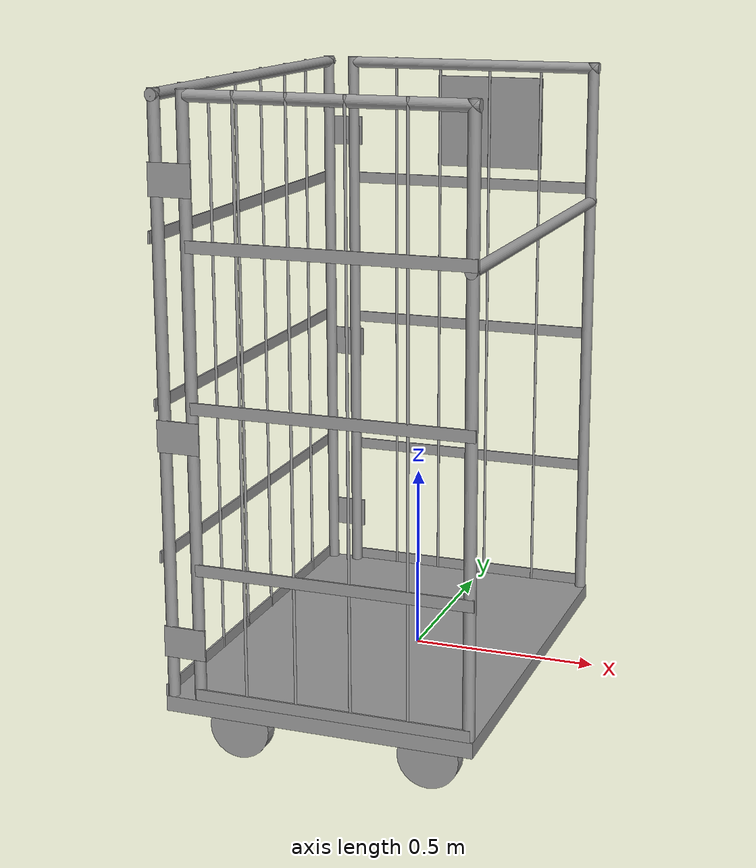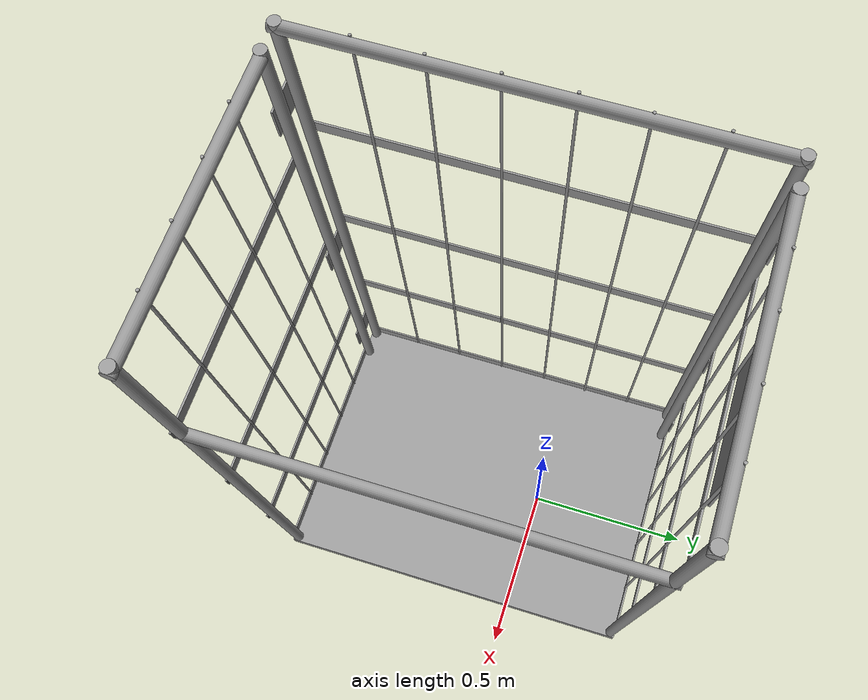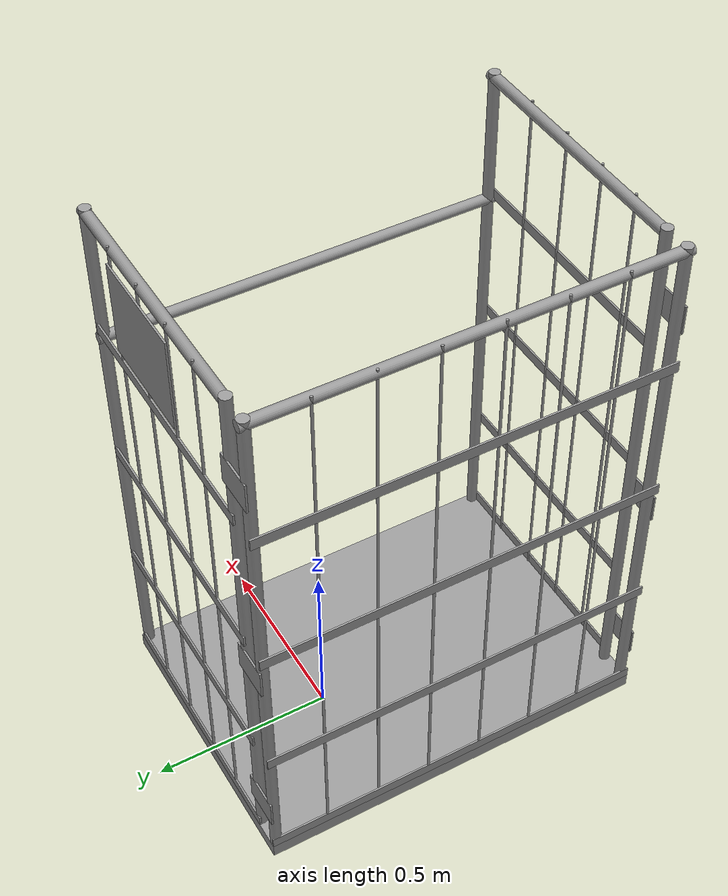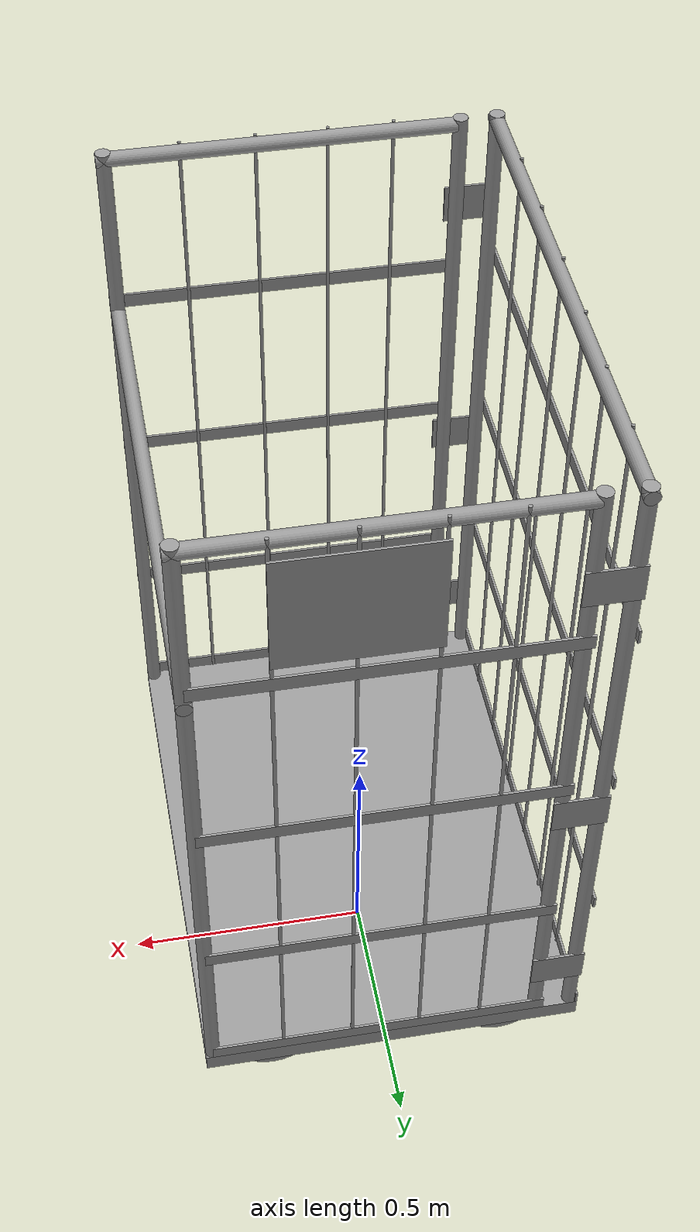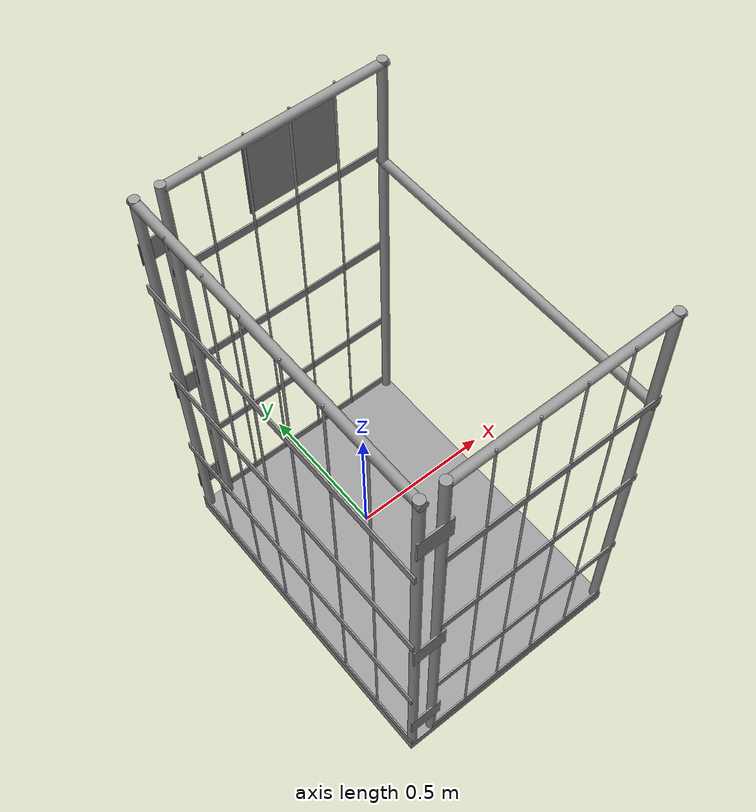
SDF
<?xml version='1.0'?>
<sdf version='1.6'>
  <model name='trolley02'>
    <model name='warehouse_trolley_with_fixed_wheels'>
      <link name='link_0_clone'>
        <pose frame=''>0.241492 -0.606629 -0.026694 1.5707 -0 0</pose>
        <inertial>
          <mass>1</mass>
          <inertia>
            <ixx>0.145833</ixx>
            <ixy>0</ixy>
            <ixz>0</ixz>
            <iyy>0.145833</iyy>
            <iyz>0</iyz>
            <izz>0.125</izz>
          </inertia>
          <pose frame=''>0 0 0 0 -0 0</pose>
        </inertial>
        <self_collide>0</self_collide>
        <kinematic>0</kinematic>
        <gravity>1</gravity>
        <visual name='visual'>
          <pose frame=''>0 0 0 0 -0 0</pose>
          <geometry>
            <cylinder>
              <radius>0.08</radius>
              <length>0.04</length>
            </cylinder>
          </geometry>
          <material>
            <lighting>1</lighting>
            <script>
              <uri>file://media/materials/scripts/gazebo.material</uri>
              <name>Gazebo/Grey</name>
            </script>
            <ambient>0.3 0.3 0.3 1</ambient>
            <diffuse>0.7 0.7 0.7 1</diffuse>
            <specular>0.01 0.01 0.01 1</specular>
            <emissive>0 0 0 1</emissive>
            <shader type='vertex'>
              <normal_map>__default__</normal_map>
            </shader>
          </material>
          <cast_shadows>1</cast_shadows>
          <transparency>0</transparency>
        </visual>
        <collision name='collision'>
          <laser_retro>0</laser_retro>
          <max_contacts>10</max_contacts>
          <pose frame=''>0 0 0 0 -0 0</pose>
          <geometry>
            <cylinder>
              <radius>0.08</radius>
              <length>0.04</length>
            </cylinder>
          </geometry>
          <surface>
            <friction>
              <ode>
                <mu>1</mu>
                <mu2>1</mu2>
                <fdir1>0 0 0</fdir1>
                <slip1>0</slip1>
                <slip2>0</slip2>
              </ode>
              <torsional>
                <coefficient>1</coefficient>
                <patch_radius>0</patch_radius>
                <surface_radius>0</surface_radius>
                <use_patch_radius>1</use_patch_radius>
                <ode>
                  <slip>0</slip>
                </ode>
              </torsional>
            </friction>
            <bounce>
              <restitution_coefficient>0</restitution_coefficient>
              <threshold>1e+06</threshold>
            </bounce>
            <contact>
              <collide_without_contact>0</collide_without_contact>
              <collide_without_contact_bitmask>1</collide_without_contact_bitmask>
              <collide_bitmask>1</collide_bitmask>
              <ode>
                <soft_cfm>0</soft_cfm>
                <soft_erp>0.2</soft_erp>
                <kp>1e+13</kp>
                <kd>1</kd>
                <max_vel>0.01</max_vel>
                <min_depth>0</min_depth>
              </ode>
              <bullet>
                <split_impulse>1</split_impulse>
                <split_impulse_penetration_threshold>-0.01</split_impulse_penetration_threshold>
                <soft_cfm>0</soft_cfm>
                <soft_erp>0.2</soft_erp>
                <kp>1e+13</kp>
                <kd>1</kd>
              </bullet>
            </contact>
          </surface>
        </collision>
      </link>
      <link name='link_0_clone_clone'>
        <pose frame=''>-0.262617 -0.607972 -0.026746 1.5707 -0 0</pose>
        <inertial>
          <mass>1</mass>
          <inertia>
            <ixx>0.145833</ixx>
            <ixy>0</ixy>
            <ixz>0</ixz>
            <iyy>0.145833</iyy>
            <iyz>0</iyz>
            <izz>0.125</izz>
          </inertia>
          <pose frame=''>0 0 0 0 -0 0</pose>
        </inertial>
        <self_collide>0</self_collide>
        <kinematic>0</kinematic>
        <visual name='visual'>
          <pose frame=''>0 0 0 0 -0 0</pose>
          <geometry>
            <cylinder>
              <radius>0.08</radius>
              <length>0.04</length>
            </cylinder>
          </geometry>
          <material>
            <lighting>1</lighting>
            <script>
              <uri>file://media/materials/scripts/gazebo.material</uri>
              <name>Gazebo/Grey</name>
            </script>
            <ambient>0.3 0.3 0.3 1</ambient>
            <diffuse>0.7 0.7 0.7 1</diffuse>
            <specular>0.01 0.01 0.01 1</specular>
            <emissive>0 0 0 1</emissive>
            <shader type='vertex'>
              <normal_map>__default__</normal_map>
            </shader>
          </material>
          <cast_shadows>1</cast_shadows>
          <transparency>0</transparency>
        </visual>
        <collision name='collision'>
          <laser_retro>0</laser_retro>
          <max_contacts>10</max_contacts>
          <pose frame=''>0 0 0 0 -0 0</pose>
          <geometry>
            <cylinder>
              <radius>0.08</radius>
              <length>0.04</length>
            </cylinder>
          </geometry>
          <surface>
            <friction>
              <ode>
                <mu>1</mu>
                <mu2>1</mu2>
                <fdir1>0 0 0</fdir1>
                <slip1>0</slip1>
                <slip2>0</slip2>
              </ode>
              <torsional>
                <coefficient>1</coefficient>
                <patch_radius>0</patch_radius>
                <surface_radius>0</surface_radius>
                <use_patch_radius>1</use_patch_radius>
                <ode>
                  <slip>0</slip>
                </ode>
              </torsional>
            </friction>
            <bounce>
              <restitution_coefficient>0</restitution_coefficient>
              <threshold>1e+06</threshold>
            </bounce>
            <contact>
              <collide_without_contact>0</collide_without_contact>
              <collide_without_contact_bitmask>1</collide_without_contact_bitmask>
              <collide_bitmask>1</collide_bitmask>
              <ode>
                <soft_cfm>0</soft_cfm>
                <soft_erp>0.2</soft_erp>
                <kp>1e+13</kp>
                <kd>1</kd>
                <max_vel>0.01</max_vel>
                <min_depth>0</min_depth>
              </ode>
              <bullet>
                <split_impulse>1</split_impulse>
                <split_impulse_penetration_threshold>-0.01</split_impulse_penetration_threshold>
                <soft_cfm>0</soft_cfm>
                <soft_erp>0.2</soft_erp>
                <kp>1e+13</kp>
                <kd>1</kd>
              </bullet>
            </contact>
          </surface>
        </collision>
      </link>
      <link name='link_0_clone_clone_0'>
        <pose frame=''>-0.268894 0.263749 -0.026637 1.5707 -0 0</pose>
        <inertial>
          <mass>1</mass>
          <inertia>
            <ixx>0.145833</ixx>
            <ixy>0</ixy>
            <ixz>0</ixz>
            <iyy>0.145833</iyy>
            <iyz>0</iyz>
            <izz>0.125</izz>
          </inertia>
          <pose frame=''>0 0 0 0 -0 0</pose>
        </inertial>
        <self_collide>0</self_collide>
        <kinematic>0</kinematic>
        <visual name='visual'>
          <pose frame=''>0 0 0 0 -0 0</pose>
          <geometry>
            <cylinder>
              <radius>0.08</radius>
              <length>0.04</length>
            </cylinder>
          </geometry>
          <material>
            <lighting>1</lighting>
            <script>
              <uri>file://media/materials/scripts/gazebo.material</uri>
              <name>Gazebo/Grey</name>
            </script>
            <ambient>0.3 0.3 0.3 1</ambient>
            <diffuse>0.7 0.7 0.7 1</diffuse>
            <specular>0.01 0.01 0.01 1</specular>
            <emissive>0 0 0 1</emissive>
            <shader type='vertex'>
              <normal_map>__default__</normal_map>
            </shader>
          </material>
          <cast_shadows>1</cast_shadows>
          <transparency>0</transparency>
        </visual>
        <collision name='collision'>
          <laser_retro>0</laser_retro>
          <max_contacts>10</max_contacts>
          <pose frame=''>0 0 0 0 -0 0</pose>
          <geometry>
            <cylinder>
              <radius>0.08</radius>
              <length>0.04</length>
            </cylinder>
          </geometry>
          <surface>
            <friction>
              <ode>
                <mu>1</mu>
                <mu2>1</mu2>
                <fdir1>0 0 0</fdir1>
                <slip1>0</slip1>
                <slip2>0</slip2>
              </ode>
              <torsional>
                <coefficient>1</coefficient>
                <patch_radius>0</patch_radius>
                <surface_radius>0</surface_radius>
                <use_patch_radius>1</use_patch_radius>
                <ode>
                  <slip>0</slip>
                </ode>
              </torsional>
            </friction>
            <bounce>
              <restitution_coefficient>0</restitution_coefficient>
              <threshold>1e+06</threshold>
            </bounce>
            <contact>
              <collide_without_contact>0</collide_without_contact>
              <collide_without_contact_bitmask>1</collide_without_contact_bitmask>
              <collide_bitmask>1</collide_bitmask>
              <ode>
                <soft_cfm>0</soft_cfm>
                <soft_erp>0.2</soft_erp>
                <kp>1e+13</kp>
                <kd>1</kd>
                <max_vel>0.01</max_vel>
                <min_depth>0</min_depth>
              </ode>
              <bullet>
                <split_impulse>1</split_impulse>
                <split_impulse_penetration_threshold>-0.01</split_impulse_penetration_threshold>
                <soft_cfm>0</soft_cfm>
                <soft_erp>0.2</soft_erp>
                <kp>1e+13</kp>
                <kd>1</kd>
              </bullet>
            </contact>
          </surface>
        </collision>
      </link>
      <link name='link_0_clone_clone_1'>
        <pose frame=''>0.239337 0.263226 -0.026637 1.5707 -0 0</pose>
        <inertial>
          <mass>1</mass>
          <inertia>
            <ixx>0.145833</ixx>
            <ixy>0</ixy>
            <ixz>0</ixz>
            <iyy>0.145833</iyy>
            <iyz>0</iyz>
            <izz>0.125</izz>
          </inertia>
          <pose frame=''>0 0 0 0 -0 0</pose>
        </inertial>
        <self_collide>0</self_collide>
        <kinematic>0</kinematic>
        <visual name='visual'>
          <pose frame=''>0 0 0 0 -0 0</pose>
          <geometry>
            <cylinder>
              <radius>0.08</radius>
              <length>0.04</length>
            </cylinder>
          </geometry>
          <material>
            <lighting>1</lighting>
            <script>
              <uri>file://media/materials/scripts/gazebo.material</uri>
              <name>Gazebo/Grey</name>
            </script>
            <ambient>0.3 0.3 0.3 1</ambient>
            <diffuse>0.7 0.7 0.7 1</diffuse>
            <specular>0.01 0.01 0.01 1</specular>
            <emissive>0 0 0 1</emissive>
            <shader type='vertex'>
              <normal_map>__default__</normal_map>
            </shader>
          </material>
          <cast_shadows>1</cast_shadows>
          <transparency>0</transparency>
        </visual>
        <collision name='collision'>
          <laser_retro>0</laser_retro>
          <max_contacts>10</max_contacts>
          <pose frame=''>0 0 0 0 -0 0</pose>
          <geometry>
            <cylinder>
              <radius>0.08</radius>
              <length>0.04</length>
            </cylinder>
          </geometry>
          <surface>
            <friction>
              <ode>
                <mu>1</mu>
                <mu2>1</mu2>
                <fdir1>0 0 0</fdir1>
                <slip1>0</slip1>
                <slip2>0</slip2>
              </ode>
              <torsional>
                <coefficient>1</coefficient>
                <patch_radius>0</patch_radius>
                <surface_radius>0</surface_radius>
                <use_patch_radius>1</use_patch_radius>
                <ode>
                  <slip>0</slip>
                </ode>
              </torsional>
            </friction>
            <bounce>
              <restitution_coefficient>0</restitution_coefficient>
              <threshold>1e+06</threshold>
            </bounce>
            <contact>
              <collide_without_contact>0</collide_without_contact>
              <collide_without_contact_bitmask>1</collide_without_contact_bitmask>
              <collide_bitmask>1</collide_bitmask>
              <ode>
                <soft_cfm>0</soft_cfm>
                <soft_erp>0.2</soft_erp>
                <kp>1e+13</kp>
                <kd>1</kd>
                <max_vel>0.01</max_vel>
                <min_depth>0</min_depth>
              </ode>
              <bullet>
                <split_impulse>1</split_impulse>
                <split_impulse_penetration_threshold>-0.01</split_impulse_penetration_threshold>
                <soft_cfm>0</soft_cfm>
                <soft_erp>0.2</soft_erp>
                <kp>1e+13</kp>
                <kd>1</kd>
              </bullet>
            </contact>
          </surface>
        </collision>
      </link>
      <model name='warehouse_trolley_without_wheels'>
        <link name='link_1'>
          <pose frame=''>-0.059879 -0.872257 -0.039145 0 -0 0</pose>
          <inertial>
            <mass>1</mass>
            <inertia>
              <ixx>0.166667</ixx>
              <ixy>0</ixy>
              <ixz>0</ixz>
              <iyy>0.166667</iyy>
              <iyz>0</iyz>
              <izz>0.166667</izz>
            </inertia>
            <pose frame=''>0 0 0 0 -0 0</pose>
          </inertial>
          <gravity>1</gravity>
          <self_collide>0</self_collide>
          <kinematic>0</kinematic>
          <visual name='visual'>
            <pose frame=''>0 0 0 0 -0 0</pose>
            <geometry>
              <box>
                <size>0.8 1.1 0.04</size>
              </box>
            </geometry>
            <material>
              <lighting>1</lighting>
              <script>
                <uri>file://media/materials/scripts/gazebo.material</uri>
                <name>Gazebo/Grey</name>
              </script>
              <ambient>0.3 0.3 0.3 1</ambient>
              <diffuse>0.7 0.7 0.7 1</diffuse>
              <specular>0.01 0.01 0.01 1</specular>
              <emissive>0 0 0 1</emissive>
              <shader type='vertex'>
                <normal_map>__default__</normal_map>
              </shader>
            </material>
            <cast_shadows>1</cast_shadows>
            <transparency>0</transparency>
          </visual>
          <collision name='collision'>
            <laser_retro>0</laser_retro>
            <max_contacts>10</max_contacts>
            <pose frame=''>0 0 0 0 -0 0</pose>
            <geometry>
              <box>
                <size>0.8 1.1 0.04</size>
              </box>
            </geometry>
            <surface>
              <friction>
                <ode>
                  <mu>1</mu>
                  <mu2>1</mu2>
                  <fdir1>0 0 0</fdir1>
                  <slip1>0</slip1>
                  <slip2>0</slip2>
                </ode>
                <torsional>
                  <coefficient>1</coefficient>
                  <patch_radius>0</patch_radius>
                  <surface_radius>0</surface_radius>
                  <use_patch_radius>1</use_patch_radius>
                  <ode>
                    <slip>0</slip>
                  </ode>
                </torsional>
              </friction>
              <bounce>
                <restitution_coefficient>0</restitution_coefficient>
                <threshold>1e+06</threshold>
              </bounce>
              <contact>
                <collide_without_contact>0</collide_without_contact>
                <collide_without_contact_bitmask>1</collide_without_contact_bitmask>
                <collide_bitmask>1</collide_bitmask>
                <ode>
                  <soft_cfm>0</soft_cfm>
                  <soft_erp>0.2</soft_erp>
                  <kp>1e+13</kp>
                  <kd>1</kd>
                  <max_vel>0.01</max_vel>
                  <min_depth>0</min_depth>
                </ode>
                <bullet>
                  <split_impulse>1</split_impulse>
                  <split_impulse_penetration_threshold>-0.01</split_impulse_penetration_threshold>
                  <soft_cfm>0</soft_cfm>
                  <soft_erp>0.2</soft_erp>
                  <kp>1e+13</kp>
                  <kd>1</kd>
                </bullet>
              </contact>
            </surface>
          </collision>
        </link>
        <link name='link_2_clone_0'>
          <pose frame=''>-0.444879 -0.337257 0.730855 0 -0 0</pose>
          <inertial>
            <mass>1</mass>
            <inertia>
              <ixx>0.145833</ixx>
              <ixy>0</ixy>
              <ixz>0</ixz>
              <iyy>0.145833</iyy>
              <iyz>0</iyz>
              <izz>0.125</izz>
            </inertia>
            <pose frame=''>0 0 0 0 -0 0</pose>
          </inertial>
          <self_collide>0</self_collide>
          <kinematic>0</kinematic>
          <visual name='visual'>
            <pose frame=''>0 0 0 0 -0 0</pose>
            <geometry>
              <cylinder>
                <radius>0.015</radius>
                <length>1.5</length>
              </cylinder>
            </geometry>
            <material>
              <lighting>1</lighting>
              <script>
                <uri>file://media/materials/scripts/gazebo.material</uri>
                <name>Gazebo/Grey</name>
              </script>
              <ambient>0.3 0.3 0.3 1</ambient>
              <diffuse>0.7 0.7 0.7 1</diffuse>
              <specular>0.01 0.01 0.01 1</specular>
              <emissive>0 0 0 1</emissive>
              <shader type='vertex'>
                <normal_map>__default__</normal_map>
              </shader>
            </material>
            <cast_shadows>1</cast_shadows>
            <transparency>0</transparency>
          </visual>
          <collision name='collision'>
            <laser_retro>0</laser_retro>
            <max_contacts>10</max_contacts>
            <pose frame=''>0 0 0 0 -0 0</pose>
            <geometry>
              <cylinder>
                <radius>0.015</radius>
                <length>1.5</length>
              </cylinder>
            </geometry>
            <surface>
              <friction>
                <ode>
                  <mu>1</mu>
                  <mu2>1</mu2>
                  <fdir1>0 0 0</fdir1>
                  <slip1>0</slip1>
                  <slip2>0</slip2>
                </ode>
                <torsional>
                  <coefficient>1</coefficient>
                  <patch_radius>0</patch_radius>
                  <surface_radius>0</surface_radius>
                  <use_patch_radius>1</use_patch_radius>
                  <ode>
                    <slip>0</slip>
                  </ode>
                </torsional>
              </friction>
              <bounce>
                <restitution_coefficient>0</restitution_coefficient>
                <threshold>1e+06</threshold>
              </bounce>
              <contact>
                <collide_without_contact>0</collide_without_contact>
                <collide_without_contact_bitmask>1</collide_without_contact_bitmask>
                <collide_bitmask>1</collide_bitmask>
                <ode>
                  <soft_cfm>0</soft_cfm>
                  <soft_erp>0.2</soft_erp>
                  <kp>1e+13</kp>
                  <kd>1</kd>
                  <max_vel>0.01</max_vel>
                  <min_depth>0</min_depth>
                </ode>
                <bullet>
                  <split_impulse>1</split_impulse>
                  <split_impulse_penetration_threshold>-0.01</split_impulse_penetration_threshold>
                  <soft_cfm>0</soft_cfm>
                  <soft_erp>0.2</soft_erp>
                  <kp>1e+13</kp>
                  <kd>1</kd>
                </bullet>
              </contact>
            </surface>
          </collision>
        </link>
        <link name='link_2_clone_0_clone'>
          <pose frame=''>-0.444879 -1.40726 0.730855 0 -0 0</pose>
          <inertial>
            <mass>1</mass>
            <inertia>
              <ixx>0.145833</ixx>
              <ixy>0</ixy>
              <ixz>0</ixz>
              <iyy>0.145833</iyy>
              <iyz>0</iyz>
              <izz>0.125</izz>
            </inertia>
            <pose frame=''>0 0 0 0 -0 0</pose>
          </inertial>
          <self_collide>0</self_collide>
          <kinematic>0</kinematic>
          <visual name='visual'>
            <pose frame=''>0 0 0 0 -0 0</pose>
            <geometry>
              <cylinder>
                <radius>0.015</radius>
                <length>1.5</length>
              </cylinder>
            </geometry>
            <material>
              <lighting>1</lighting>
              <script>
                <uri>file://media/materials/scripts/gazebo.material</uri>
                <name>Gazebo/Grey</name>
              </script>
              <ambient>0.3 0.3 0.3 1</ambient>
              <diffuse>0.7 0.7 0.7 1</diffuse>
              <specular>0.01 0.01 0.01 1</specular>
              <emissive>0 0 0 1</emissive>
              <shader type='vertex'>
                <normal_map>__default__</normal_map>
              </shader>
            </material>
            <cast_shadows>1</cast_shadows>
            <transparency>0</transparency>
          </visual>
          <collision name='collision'>
            <laser_retro>0</laser_retro>
            <max_contacts>10</max_contacts>
            <pose frame=''>0 0 0 0 -0 0</pose>
            <geometry>
              <cylinder>
                <radius>0.015</radius>
                <length>1.5</length>
              </cylinder>
            </geometry>
            <surface>
              <friction>
                <ode>
                  <mu>1</mu>
                  <mu2>1</mu2>
                  <fdir1>0 0 0</fdir1>
                  <slip1>0</slip1>
                  <slip2>0</slip2>
                </ode>
                <torsional>
                  <coefficient>1</coefficient>
                  <patch_radius>0</patch_radius>
                  <surface_radius>0</surface_radius>
                  <use_patch_radius>1</use_patch_radius>
                  <ode>
                    <slip>0</slip>
                  </ode>
                </torsional>
              </friction>
              <bounce>
                <restitution_coefficient>0</restitution_coefficient>
                <threshold>1e+06</threshold>
              </bounce>
              <contact>
                <collide_without_contact>0</collide_without_contact>
                <collide_without_contact_bitmask>1</collide_without_contact_bitmask>
                <collide_bitmask>1</collide_bitmask>
                <ode>
                  <soft_cfm>0</soft_cfm>
                  <soft_erp>0.2</soft_erp>
                  <kp>1e+13</kp>
                  <kd>1</kd>
                  <max_vel>0.01</max_vel>
                  <min_depth>0</min_depth>
                </ode>
                <bullet>
                  <split_impulse>1</split_impulse>
                  <split_impulse_penetration_threshold>-0.01</split_impulse_penetration_threshold>
                  <soft_cfm>0</soft_cfm>
                  <soft_erp>0.2</soft_erp>
                  <kp>1e+13</kp>
                  <kd>1</kd>
                </bullet>
              </contact>
            </surface>
          </collision>
        </link>
        <link name='link_2_clone_0_clone_0'>
          <pose frame=''>-0.371796 -1.40726 0.730855 0 -0 0</pose>
          <inertial>
            <mass>1</mass>
            <inertia>
              <ixx>0.145833</ixx>
              <ixy>0</ixy>
              <ixz>0</ixz>
              <iyy>0.145833</iyy>
              <iyz>0</iyz>
              <izz>0.125</izz>
            </inertia>
            <pose frame=''>0 0 0 0 -0 0</pose>
          </inertial>
          <self_collide>0</self_collide>
          <kinematic>0</kinematic>
          <visual name='visual'>
            <pose frame=''>0 0 0 0 -0 0</pose>
            <geometry>
              <cylinder>
                <radius>0.015</radius>
                <length>1.5</length>
              </cylinder>
            </geometry>
            <material>
              <lighting>1</lighting>
              <script>
                <uri>file://media/materials/scripts/gazebo.material</uri>
                <name>Gazebo/Grey</name>
              </script>
              <ambient>0.3 0.3 0.3 1</ambient>
              <diffuse>0.7 0.7 0.7 1</diffuse>
              <specular>0.01 0.01 0.01 1</specular>
              <emissive>0 0 0 1</emissive>
              <shader type='vertex'>
                <normal_map>__default__</normal_map>
              </shader>
            </material>
            <cast_shadows>1</cast_shadows>
            <transparency>0</transparency>
          </visual>
          <collision name='collision'>
            <laser_retro>0</laser_retro>
            <max_contacts>10</max_contacts>
            <pose frame=''>0 0 0 0 -0 0</pose>
            <geometry>
              <cylinder>
                <radius>0.015</radius>
                <length>1.5</length>
              </cylinder>
            </geometry>
            <surface>
              <friction>
                <ode>
                  <mu>1</mu>
                  <mu2>1</mu2>
                  <fdir1>0 0 0</fdir1>
                  <slip1>0</slip1>
                  <slip2>0</slip2>
                </ode>
                <torsional>
                  <coefficient>1</coefficient>
                  <patch_radius>0</patch_radius>
                  <surface_radius>0</surface_radius>
                  <use_patch_radius>1</use_patch_radius>
                  <ode>
                    <slip>0</slip>
                  </ode>
                </torsional>
              </friction>
              <bounce>
                <restitution_coefficient>0</restitution_coefficient>
                <threshold>1e+06</threshold>
              </bounce>
              <contact>
                <collide_without_contact>0</collide_without_contact>
                <collide_without_contact_bitmask>1</collide_without_contact_bitmask>
                <collide_bitmask>1</collide_bitmask>
                <ode>
                  <soft_cfm>0</soft_cfm>
                  <soft_erp>0.2</soft_erp>
                  <kp>1e+13</kp>
                  <kd>1</kd>
                  <max_vel>0.01</max_vel>
                  <min_depth>0</min_depth>
                </ode>
                <bullet>
                  <split_impulse>1</split_impulse>
                  <split_impulse_penetration_threshold>-0.01</split_impulse_penetration_threshold>
                  <soft_cfm>0</soft_cfm>
                  <soft_erp>0.2</soft_erp>
                  <kp>1e+13</kp>
                  <kd>1</kd>
                </bullet>
              </contact>
            </surface>
          </collision>
        </link>
        <link name='link_2_clone_0_clone_1'>
          <pose frame=''>0.325121 -1.40726 0.730855 0 -0 0</pose>
          <inertial>
            <mass>1</mass>
            <inertia>
              <ixx>0.145833</ixx>
              <ixy>0</ixy>
              <ixz>0</ixz>
              <iyy>0.145833</iyy>
              <iyz>0</iyz>
              <izz>0.125</izz>
            </inertia>
            <pose frame=''>0 0 0 0 -0 0</pose>
          </inertial>
          <self_collide>0</self_collide>
          <kinematic>0</kinematic>
          <visual name='visual'>
            <pose frame=''>0 0 0 0 -0 0</pose>
            <geometry>
              <cylinder>
                <radius>0.015</radius>
                <length>1.5</length>
              </cylinder>
            </geometry>
            <material>
              <lighting>1</lighting>
              <script>
                <uri>file://media/materials/scripts/gazebo.material</uri>
                <name>Gazebo/Grey</name>
              </script>
              <ambient>0.3 0.3 0.3 1</ambient>
              <diffuse>0.7 0.7 0.7 1</diffuse>
              <specular>0.01 0.01 0.01 1</specular>
              <emissive>0 0 0 1</emissive>
              <shader type='vertex'>
                <normal_map>__default__</normal_map>
              </shader>
            </material>
            <cast_shadows>1</cast_shadows>
            <transparency>0</transparency>
          </visual>
          <collision name='collision'>
            <laser_retro>0</laser_retro>
            <max_contacts>10</max_contacts>
            <pose frame=''>0 0 0 0 -0 0</pose>
            <geometry>
              <cylinder>
                <radius>0.015</radius>
                <length>1.5</length>
              </cylinder>
            </geometry>
            <surface>
              <friction>
                <ode>
                  <mu>1</mu>
                  <mu2>1</mu2>
                  <fdir1>0 0 0</fdir1>
                  <slip1>0</slip1>
                  <slip2>0</slip2>
                </ode>
                <torsional>
                  <coefficient>1</coefficient>
                  <patch_radius>0</patch_radius>
                  <surface_radius>0</surface_radius>
                  <use_patch_radius>1</use_patch_radius>
                  <ode>
                    <slip>0</slip>
                  </ode>
                </torsional>
              </friction>
              <bounce>
                <restitution_coefficient>0</restitution_coefficient>
                <threshold>1e+06</threshold>
              </bounce>
              <contact>
                <collide_without_contact>0</collide_without_contact>
                <collide_without_contact_bitmask>1</collide_without_contact_bitmask>
                <collide_bitmask>1</collide_bitmask>
                <ode>
                  <soft_cfm>0</soft_cfm>
                  <soft_erp>0.2</soft_erp>
                  <kp>1e+13</kp>
                  <kd>1</kd>
                  <max_vel>0.01</max_vel>
                  <min_depth>0</min_depth>
                </ode>
                <bullet>
                  <split_impulse>1</split_impulse>
                  <split_impulse_penetration_threshold>-0.01</split_impulse_penetration_threshold>
                  <soft_cfm>0</soft_cfm>
                  <soft_erp>0.2</soft_erp>
                  <kp>1e+13</kp>
                  <kd>1</kd>
                </bullet>
              </contact>
            </surface>
          </collision>
        </link>
        <link name='link_2_clone_0_clone_clone'>
          <pose frame=''>0.177056 -1.41876 0.730855 0 -0 0</pose>
          <inertial>
            <mass>1</mass>
            <inertia>
              <ixx>0.145833</ixx>
              <ixy>0</ixy>
              <ixz>0</ixz>
              <iyy>0.145833</iyy>
              <iyz>0</iyz>
              <izz>0.125</izz>
            </inertia>
            <pose frame=''>0 0 0 0 -0 0</pose>
          </inertial>
          <self_collide>0</self_collide>
          <kinematic>0</kinematic>
          <gravity>1</gravity>
          <visual name='visual'>
            <pose frame=''>0 0 0 0 -0 0</pose>
            <geometry>
              <cylinder>
                <radius>0.0035</radius>
                <length>1.5</length>
              </cylinder>
            </geometry>
            <material>
              <lighting>1</lighting>
              <script>
                <uri>file://media/materials/scripts/gazebo.material</uri>
                <name>Gazebo/Grey</name>
              </script>
              <ambient>0.3 0.3 0.3 1</ambient>
              <diffuse>0.7 0.7 0.7 1</diffuse>
              <specular>0.01 0.01 0.01 1</specular>
              <emissive>0 0 0 1</emissive>
              <shader type='vertex'>
                <normal_map>__default__</normal_map>
              </shader>
            </material>
            <cast_shadows>1</cast_shadows>
            <transparency>0</transparency>
          </visual>
          <collision name='collision'>
            <laser_retro>0</laser_retro>
            <max_contacts>10</max_contacts>
            <pose frame=''>0 0 0 0 -0 0</pose>
            <geometry>
              <cylinder>
                <radius>0.0035</radius>
                <length>1.5</length>
              </cylinder>
            </geometry>
            <surface>
              <friction>
                <ode>
                  <mu>1</mu>
                  <mu2>1</mu2>
                  <fdir1>0 0 0</fdir1>
                  <slip1>0</slip1>
                  <slip2>0</slip2>
                </ode>
                <torsional>
                  <coefficient>1</coefficient>
                  <patch_radius>0</patch_radius>
                  <surface_radius>0</surface_radius>
                  <use_patch_radius>1</use_patch_radius>
                  <ode>
                    <slip>0</slip>
                  </ode>
                </torsional>
              </friction>
              <bounce>
                <restitution_coefficient>0</restitution_coefficient>
                <threshold>1e+06</threshold>
              </bounce>
              <contact>
                <collide_without_contact>0</collide_without_contact>
                <collide_without_contact_bitmask>1</collide_without_contact_bitmask>
                <collide_bitmask>1</collide_bitmask>
                <ode>
                  <soft_cfm>0</soft_cfm>
                  <soft_erp>0.2</soft_erp>
                  <kp>1e+13</kp>
                  <kd>1</kd>
                  <max_vel>0.01</max_vel>
                  <min_depth>0</min_depth>
                </ode>
                <bullet>
                  <split_impulse>1</split_impulse>
                  <split_impulse_penetration_threshold>-0.01</split_impulse_penetration_threshold>
                  <soft_cfm>0</soft_cfm>
                  <soft_erp>0.2</soft_erp>
                  <kp>1e+13</kp>
                  <kd>1</kd>
                </bullet>
              </contact>
            </surface>
          </collision>
        </link>
        <link name='link_2_clone_0_clone_clone_clone'>
          <pose frame=''>-0.241474 -1.41876 0.730855 0 -0 0</pose>
          <inertial>
            <mass>1</mass>
            <inertia>
              <ixx>0.145833</ixx>
              <ixy>0</ixy>
              <ixz>0</ixz>
              <iyy>0.145833</iyy>
              <iyz>0</iyz>
              <izz>0.125</izz>
            </inertia>
            <pose frame=''>0 0 0 0 -0 0</pose>
          </inertial>
          <self_collide>0</self_collide>
          <kinematic>0</kinematic>
          <visual name='visual'>
            <pose frame=''>0 0 0 0 -0 0</pose>
            <geometry>
              <cylinder>
                <radius>0.0035</radius>
                <length>1.5</length>
              </cylinder>
            </geometry>
            <material>
              <lighting>1</lighting>
              <script>
                <uri>file://media/materials/scripts/gazebo.material</uri>
                <name>Gazebo/Grey</name>
              </script>
              <ambient>0.3 0.3 0.3 1</ambient>
              <diffuse>0.7 0.7 0.7 1</diffuse>
              <specular>0.01 0.01 0.01 1</specular>
              <emissive>0 0 0 1</emissive>
              <shader type='vertex'>
                <normal_map>__default__</normal_map>
              </shader>
            </material>
            <cast_shadows>1</cast_shadows>
            <transparency>0</transparency>
          </visual>
          <collision name='collision'>
            <laser_retro>0</laser_retro>
            <max_contacts>10</max_contacts>
            <pose frame=''>0 0 0 0 -0 0</pose>
            <geometry>
              <cylinder>
                <radius>0.0035</radius>
                <length>1.5</length>
              </cylinder>
            </geometry>
            <surface>
              <friction>
                <ode>
                  <mu>1</mu>
                  <mu2>1</mu2>
                  <fdir1>0 0 0</fdir1>
                  <slip1>0</slip1>
                  <slip2>0</slip2>
                </ode>
                <torsional>
                  <coefficient>1</coefficient>
                  <patch_radius>0</patch_radius>
                  <surface_radius>0</surface_radius>
                  <use_patch_radius>1</use_patch_radius>
                  <ode>
                    <slip>0</slip>
                  </ode>
                </torsional>
              </friction>
              <bounce>
                <restitution_coefficient>0</restitution_coefficient>
                <threshold>1e+06</threshold>
              </bounce>
              <contact>
                <collide_without_contact>0</collide_without_contact>
                <collide_without_contact_bitmask>1</collide_without_contact_bitmask>
                <collide_bitmask>1</collide_bitmask>
                <ode>
                  <soft_cfm>0</soft_cfm>
                  <soft_erp>0.2</soft_erp>
                  <kp>1e+13</kp>
                  <kd>1</kd>
                  <max_vel>0.01</max_vel>
                  <min_depth>0</min_depth>
                </ode>
                <bullet>
                  <split_impulse>1</split_impulse>
                  <split_impulse_penetration_threshold>-0.01</split_impulse_penetration_threshold>
                  <soft_cfm>0</soft_cfm>
                  <soft_erp>0.2</soft_erp>
                  <kp>1e+13</kp>
                  <kd>1</kd>
                </bullet>
              </contact>
            </surface>
          </collision>
        </link>
        <link name='link_2_clone_0_clone_clone_clone_0'>
          <pose frame=''>-0.111662 -1.41876 0.730855 0 -0 0</pose>
          <inertial>
            <mass>1</mass>
            <inertia>
              <ixx>0.145833</ixx>
              <ixy>0</ixy>
              <ixz>0</ixz>
              <iyy>0.145833</iyy>
              <iyz>0</iyz>
              <izz>0.125</izz>
            </inertia>
            <pose frame=''>0 0 0 0 -0 0</pose>
          </inertial>
          <self_collide>0</self_collide>
          <kinematic>0</kinematic>
          <visual name='visual'>
            <pose frame=''>0 0 0 0 -0 0</pose>
            <geometry>
              <cylinder>
                <radius>0.0035</radius>
                <length>1.5</length>
              </cylinder>
            </geometry>
            <material>
              <lighting>1</lighting>
              <script>
                <uri>file://media/materials/scripts/gazebo.material</uri>
                <name>Gazebo/Grey</name>
              </script>
              <ambient>0.3 0.3 0.3 1</ambient>
              <diffuse>0.7 0.7 0.7 1</diffuse>
              <specular>0.01 0.01 0.01 1</specular>
              <emissive>0 0 0 1</emissive>
              <shader type='vertex'>
                <normal_map>__default__</normal_map>
              </shader>
            </material>
            <cast_shadows>1</cast_shadows>
            <transparency>0</transparency>
          </visual>
          <collision name='collision'>
            <laser_retro>0</laser_retro>
            <max_contacts>10</max_contacts>
            <pose frame=''>0 0 0 0 -0 0</pose>
            <geometry>
              <cylinder>
                <radius>0.0035</radius>
                <length>1.5</length>
              </cylinder>
            </geometry>
            <surface>
              <friction>
                <ode>
                  <mu>1</mu>
                  <mu2>1</mu2>
                  <fdir1>0 0 0</fdir1>
                  <slip1>0</slip1>
                  <slip2>0</slip2>
                </ode>
                <torsional>
                  <coefficient>1</coefficient>
                  <patch_radius>0</patch_radius>
                  <surface_radius>0</surface_radius>
                  <use_patch_radius>1</use_patch_radius>
                  <ode>
                    <slip>0</slip>
                  </ode>
                </torsional>
              </friction>
              <bounce>
                <restitution_coefficient>0</restitution_coefficient>
                <threshold>1e+06</threshold>
              </bounce>
              <contact>
                <collide_without_contact>0</collide_without_contact>
                <collide_without_contact_bitmask>1</collide_without_contact_bitmask>
                <collide_bitmask>1</collide_bitmask>
                <ode>
                  <soft_cfm>0</soft_cfm>
                  <soft_erp>0.2</soft_erp>
                  <kp>1e+13</kp>
                  <kd>1</kd>
                  <max_vel>0.01</max_vel>
                  <min_depth>0</min_depth>
                </ode>
                <bullet>
                  <split_impulse>1</split_impulse>
                  <split_impulse_penetration_threshold>-0.01</split_impulse_penetration_threshold>
                  <soft_cfm>0</soft_cfm>
                  <soft_erp>0.2</soft_erp>
                  <kp>1e+13</kp>
                  <kd>1</kd>
                </bullet>
              </contact>
            </surface>
          </collision>
        </link>
        <link name='link_2_clone_0_clone_clone_clone_1'>
          <pose frame=''>0.029865 -1.41876 0.730855 0 -0 0</pose>
          <inertial>
            <mass>1</mass>
            <inertia>
              <ixx>0.145833</ixx>
              <ixy>0</ixy>
              <ixz>0</ixz>
              <iyy>0.145833</iyy>
              <iyz>0</iyz>
              <izz>0.125</izz>
            </inertia>
            <pose frame=''>0 0 0 0 -0 0</pose>
          </inertial>
          <self_collide>0</self_collide>
          <kinematic>0</kinematic>
          <visual name='visual'>
            <pose frame=''>0 0 0 0 -0 0</pose>
            <geometry>
              <cylinder>
                <radius>0.0035</radius>
                <length>1.5</length>
              </cylinder>
            </geometry>
            <material>
              <lighting>1</lighting>
              <script>
                <uri>file://media/materials/scripts/gazebo.material</uri>
                <name>Gazebo/Grey</name>
              </script>
              <ambient>0.3 0.3 0.3 1</ambient>
              <diffuse>0.7 0.7 0.7 1</diffuse>
              <specular>0.01 0.01 0.01 1</specular>
              <emissive>0 0 0 1</emissive>
              <shader type='vertex'>
                <normal_map>__default__</normal_map>
              </shader>
            </material>
            <cast_shadows>1</cast_shadows>
            <transparency>0</transparency>
          </visual>
          <collision name='collision'>
            <laser_retro>0</laser_retro>
            <max_contacts>10</max_contacts>
            <pose frame=''>0 0 0 0 -0 0</pose>
            <geometry>
              <cylinder>
                <radius>0.0035</radius>
                <length>1.5</length>
              </cylinder>
            </geometry>
            <surface>
              <friction>
                <ode>
                  <mu>1</mu>
                  <mu2>1</mu2>
                  <fdir1>0 0 0</fdir1>
                  <slip1>0</slip1>
                  <slip2>0</slip2>
                </ode>
                <torsional>
                  <coefficient>1</coefficient>
                  <patch_radius>0</patch_radius>
                  <surface_radius>0</surface_radius>
                  <use_patch_radius>1</use_patch_radius>
                  <ode>
                    <slip>0</slip>
                  </ode>
                </torsional>
              </friction>
              <bounce>
                <restitution_coefficient>0</restitution_coefficient>
                <threshold>1e+06</threshold>
              </bounce>
              <contact>
                <collide_without_contact>0</collide_without_contact>
                <collide_without_contact_bitmask>1</collide_without_contact_bitmask>
                <collide_bitmask>1</collide_bitmask>
                <ode>
                  <soft_cfm>0</soft_cfm>
                  <soft_erp>0.2</soft_erp>
                  <kp>1e+13</kp>
                  <kd>1</kd>
                  <max_vel>0.01</max_vel>
                  <min_depth>0</min_depth>
                </ode>
                <bullet>
                  <split_impulse>1</split_impulse>
                  <split_impulse_penetration_threshold>-0.01</split_impulse_penetration_threshold>
                  <soft_cfm>0</soft_cfm>
                  <soft_erp>0.2</soft_erp>
                  <kp>1e+13</kp>
                  <kd>1</kd>
                </bullet>
              </contact>
            </surface>
          </collision>
        </link>
        <link name='link_2_clone_0_clone_clone_clone_10'>
          <pose frame=''>-0.456379 -0.9395 0.730855 0 -0 0</pose>
          <inertial>
            <mass>1</mass>
            <inertia>
              <ixx>0.145833</ixx>
              <ixy>0</ixy>
              <ixz>0</ixz>
              <iyy>0.145833</iyy>
              <iyz>0</iyz>
              <izz>0.125</izz>
            </inertia>
            <pose frame=''>0 0 0 0 -0 0</pose>
          </inertial>
          <self_collide>0</self_collide>
          <kinematic>0</kinematic>
          <visual name='visual'>
            <pose frame=''>0 0 0 0 -0 0</pose>
            <geometry>
              <cylinder>
                <radius>0.0035</radius>
                <length>1.5</length>
              </cylinder>
            </geometry>
            <material>
              <lighting>1</lighting>
              <script>
                <uri>file://media/materials/scripts/gazebo.material</uri>
                <name>Gazebo/Grey</name>
              </script>
              <ambient>0.3 0.3 0.3 1</ambient>
              <diffuse>0.7 0.7 0.7 1</diffuse>
              <specular>0.01 0.01 0.01 1</specular>
              <emissive>0 0 0 1</emissive>
              <shader type='vertex'>
                <normal_map>__default__</normal_map>
              </shader>
            </material>
            <cast_shadows>1</cast_shadows>
            <transparency>0</transparency>
          </visual>
          <collision name='collision'>
            <laser_retro>0</laser_retro>
            <max_contacts>10</max_contacts>
            <pose frame=''>0 0 0 0 -0 0</pose>
            <geometry>
              <cylinder>
                <radius>0.0035</radius>
                <length>1.5</length>
              </cylinder>
            </geometry>
            <surface>
              <friction>
                <ode>
                  <mu>1</mu>
                  <mu2>1</mu2>
                  <fdir1>0 0 0</fdir1>
                  <slip1>0</slip1>
                  <slip2>0</slip2>
                </ode>
                <torsional>
                  <coefficient>1</coefficient>
                  <patch_radius>0</patch_radius>
                  <surface_radius>0</surface_radius>
                  <use_patch_radius>1</use_patch_radius>
                  <ode>
                    <slip>0</slip>
                  </ode>
                </torsional>
              </friction>
              <bounce>
                <restitution_coefficient>0</restitution_coefficient>
                <threshold>1e+06</threshold>
              </bounce>
              <contact>
                <collide_without_contact>0</collide_without_contact>
                <collide_without_contact_bitmask>1</collide_without_contact_bitmask>
                <collide_bitmask>1</collide_bitmask>
                <ode>
                  <soft_cfm>0</soft_cfm>
                  <soft_erp>0.2</soft_erp>
                  <kp>1e+13</kp>
                  <kd>1</kd>
                  <max_vel>0.01</max_vel>
                  <min_depth>0</min_depth>
                </ode>
                <bullet>
                  <split_impulse>1</split_impulse>
                  <split_impulse_penetration_threshold>-0.01</split_impulse_penetration_threshold>
                  <soft_cfm>0</soft_cfm>
                  <soft_erp>0.2</soft_erp>
                  <kp>1e+13</kp>
                  <kd>1</kd>
                </bullet>
              </contact>
            </surface>
          </collision>
        </link>
        <link name='link_2_clone_0_clone_clone_clone_11'>
          <pose frame=''>-0.456379 -1.2522 0.730855 0 -0 0</pose>
          <inertial>
            <mass>1</mass>
            <inertia>
              <ixx>0.145833</ixx>
              <ixy>0</ixy>
              <ixz>0</ixz>
              <iyy>0.145833</iyy>
              <iyz>0</iyz>
              <izz>0.125</izz>
            </inertia>
            <pose frame=''>0 0 0 0 -0 0</pose>
          </inertial>
          <self_collide>0</self_collide>
          <kinematic>0</kinematic>
          <visual name='visual'>
            <pose frame=''>0 0 0 0 -0 0</pose>
            <geometry>
              <cylinder>
                <radius>0.0035</radius>
                <length>1.5</length>
              </cylinder>
            </geometry>
            <material>
              <lighting>1</lighting>
              <script>
                <uri>file://media/materials/scripts/gazebo.material</uri>
                <name>Gazebo/Grey</name>
              </script>
              <ambient>0.3 0.3 0.3 1</ambient>
              <diffuse>0.7 0.7 0.7 1</diffuse>
              <specular>0.01 0.01 0.01 1</specular>
              <emissive>0 0 0 1</emissive>
              <shader type='vertex'>
                <normal_map>__default__</normal_map>
              </shader>
            </material>
            <cast_shadows>1</cast_shadows>
            <transparency>0</transparency>
          </visual>
          <collision name='collision'>
            <laser_retro>0</laser_retro>
            <max_contacts>10</max_contacts>
            <pose frame=''>0 0 0 0 -0 0</pose>
            <geometry>
              <cylinder>
                <radius>0.0035</radius>
                <length>1.5</length>
              </cylinder>
            </geometry>
            <surface>
              <friction>
                <ode>
                  <mu>1</mu>
                  <mu2>1</mu2>
                  <fdir1>0 0 0</fdir1>
                  <slip1>0</slip1>
                  <slip2>0</slip2>
                </ode>
                <torsional>
                  <coefficient>1</coefficient>
                  <patch_radius>0</patch_radius>
                  <surface_radius>0</surface_radius>
                  <use_patch_radius>1</use_patch_radius>
                  <ode>
                    <slip>0</slip>
                  </ode>
                </torsional>
              </friction>
              <bounce>
                <restitution_coefficient>0</restitution_coefficient>
                <threshold>1e+06</threshold>
              </bounce>
              <contact>
                <collide_without_contact>0</collide_without_contact>
                <collide_without_contact_bitmask>1</collide_without_contact_bitmask>
                <collide_bitmask>1</collide_bitmask>
                <ode>
                  <soft_cfm>0</soft_cfm>
                  <soft_erp>0.2</soft_erp>
                  <kp>1e+13</kp>
                  <kd>1</kd>
                  <max_vel>0.01</max_vel>
                  <min_depth>0</min_depth>
                </ode>
                <bullet>
                  <split_impulse>1</split_impulse>
                  <split_impulse_penetration_threshold>-0.01</split_impulse_penetration_threshold>
                  <soft_cfm>0</soft_cfm>
                  <soft_erp>0.2</soft_erp>
                  <kp>1e+13</kp>
                  <kd>1</kd>
                </bullet>
              </contact>
            </surface>
          </collision>
        </link>
        <link name='link_2_clone_0_clone_clone_clone_2'>
          <pose frame=''>0.175078 -0.325757 0.730855 0 -0 0</pose>
          <inertial>
            <mass>1</mass>
            <inertia>
              <ixx>0.145833</ixx>
              <ixy>0</ixy>
              <ixz>0</ixz>
              <iyy>0.145833</iyy>
              <iyz>0</iyz>
              <izz>0.125</izz>
            </inertia>
            <pose frame=''>0 0 0 0 -0 0</pose>
          </inertial>
          <self_collide>0</self_collide>
          <kinematic>0</kinematic>
          <visual name='visual'>
            <pose frame=''>0 0 0 0 -0 0</pose>
            <geometry>
              <cylinder>
                <radius>0.0035</radius>
                <length>1.5</length>
              </cylinder>
            </geometry>
            <material>
              <lighting>1</lighting>
              <script>
                <uri>file://media/materials/scripts/gazebo.material</uri>
                <name>Gazebo/Grey</name>
              </script>
              <ambient>0.3 0.3 0.3 1</ambient>
              <diffuse>0.7 0.7 0.7 1</diffuse>
              <specular>0.01 0.01 0.01 1</specular>
              <emissive>0 0 0 1</emissive>
              <shader type='vertex'>
                <normal_map>__default__</normal_map>
              </shader>
            </material>
            <cast_shadows>1</cast_shadows>
            <transparency>0</transparency>
          </visual>
          <collision name='collision'>
            <laser_retro>0</laser_retro>
            <max_contacts>10</max_contacts>
            <pose frame=''>0 0 0 0 -0 0</pose>
            <geometry>
              <cylinder>
                <radius>0.0035</radius>
                <length>1.5</length>
              </cylinder>
            </geometry>
            <surface>
              <friction>
                <ode>
                  <mu>1</mu>
                  <mu2>1</mu2>
                  <fdir1>0 0 0</fdir1>
                  <slip1>0</slip1>
                  <slip2>0</slip2>
                </ode>
                <torsional>
                  <coefficient>1</coefficient>
                  <patch_radius>0</patch_radius>
                  <surface_radius>0</surface_radius>
                  <use_patch_radius>1</use_patch_radius>
                  <ode>
                    <slip>0</slip>
                  </ode>
                </torsional>
              </friction>
              <bounce>
                <restitution_coefficient>0</restitution_coefficient>
                <threshold>1e+06</threshold>
              </bounce>
              <contact>
                <collide_without_contact>0</collide_without_contact>
                <collide_without_contact_bitmask>1</collide_without_contact_bitmask>
                <collide_bitmask>1</collide_bitmask>
                <ode>
                  <soft_cfm>0</soft_cfm>
                  <soft_erp>0.2</soft_erp>
                  <kp>1e+13</kp>
                  <kd>1</kd>
                  <max_vel>0.01</max_vel>
                  <min_depth>0</min_depth>
                </ode>
                <bullet>
                  <split_impulse>1</split_impulse>
                  <split_impulse_penetration_threshold>-0.01</split_impulse_penetration_threshold>
                  <soft_cfm>0</soft_cfm>
                  <soft_erp>0.2</soft_erp>
                  <kp>1e+13</kp>
                  <kd>1</kd>
                </bullet>
              </contact>
            </surface>
          </collision>
        </link>
        <link name='link_2_clone_0_clone_clone_clone_3'>
          <pose frame=''>0.028916 -0.325757 0.730855 0 -0 0</pose>
          <inertial>
            <mass>1</mass>
            <inertia>
              <ixx>0.145833</ixx>
              <ixy>0</ixy>
              <ixz>0</ixz>
              <iyy>0.145833</iyy>
              <iyz>0</iyz>
              <izz>0.125</izz>
            </inertia>
            <pose frame=''>0 0 0 0 -0 0</pose>
          </inertial>
          <self_collide>0</self_collide>
          <kinematic>0</kinematic>
          <visual name='visual'>
            <pose frame=''>0 0 0 0 -0 0</pose>
            <geometry>
              <cylinder>
                <radius>0.0035</radius>
                <length>1.5</length>
              </cylinder>
            </geometry>
            <material>
              <lighting>1</lighting>
              <script>
                <uri>file://media/materials/scripts/gazebo.material</uri>
                <name>Gazebo/Grey</name>
              </script>
              <ambient>0.3 0.3 0.3 1</ambient>
              <diffuse>0.7 0.7 0.7 1</diffuse>
              <specular>0.01 0.01 0.01 1</specular>
              <emissive>0 0 0 1</emissive>
              <shader type='vertex'>
                <normal_map>__default__</normal_map>
              </shader>
            </material>
            <cast_shadows>1</cast_shadows>
            <transparency>0</transparency>
          </visual>
          <collision name='collision'>
            <laser_retro>0</laser_retro>
            <max_contacts>10</max_contacts>
            <pose frame=''>0 0 0 0 -0 0</pose>
            <geometry>
              <cylinder>
                <radius>0.0035</radius>
                <length>1.5</length>
              </cylinder>
            </geometry>
            <surface>
              <friction>
                <ode>
                  <mu>1</mu>
                  <mu2>1</mu2>
                  <fdir1>0 0 0</fdir1>
                  <slip1>0</slip1>
                  <slip2>0</slip2>
                </ode>
                <torsional>
                  <coefficient>1</coefficient>
                  <patch_radius>0</patch_radius>
                  <surface_radius>0</surface_radius>
                  <use_patch_radius>1</use_patch_radius>
                  <ode>
                    <slip>0</slip>
                  </ode>
                </torsional>
              </friction>
              <bounce>
                <restitution_coefficient>0</restitution_coefficient>
                <threshold>1e+06</threshold>
              </bounce>
              <contact>
                <collide_without_contact>0</collide_without_contact>
                <collide_without_contact_bitmask>1</collide_without_contact_bitmask>
                <collide_bitmask>1</collide_bitmask>
                <ode>
                  <soft_cfm>0</soft_cfm>
                  <soft_erp>0.2</soft_erp>
                  <kp>1e+13</kp>
                  <kd>1</kd>
                  <max_vel>0.01</max_vel>
                  <min_depth>0</min_depth>
                </ode>
                <bullet>
                  <split_impulse>1</split_impulse>
                  <split_impulse_penetration_threshold>-0.01</split_impulse_penetration_threshold>
                  <soft_cfm>0</soft_cfm>
                  <soft_erp>0.2</soft_erp>
                  <kp>1e+13</kp>
                  <kd>1</kd>
                </bullet>
              </contact>
            </surface>
          </collision>
        </link>
        <link name='link_2_clone_0_clone_clone_clone_4'>
          <pose frame=''>-0.114759 -0.325757 0.730855 0 -0 0</pose>
          <inertial>
            <mass>1</mass>
            <inertia>
              <ixx>0.145833</ixx>
              <ixy>0</ixy>
              <ixz>0</ixz>
              <iyy>0.145833</iyy>
              <iyz>0</iyz>
              <izz>0.125</izz>
            </inertia>
            <pose frame=''>0 0 0 0 -0 0</pose>
          </inertial>
          <self_collide>0</self_collide>
          <kinematic>0</kinematic>
          <visual name='visual'>
            <pose frame=''>0 0 0 0 -0 0</pose>
            <geometry>
              <cylinder>
                <radius>0.0035</radius>
                <length>1.5</length>
              </cylinder>
            </geometry>
            <material>
              <lighting>1</lighting>
              <script>
                <uri>file://media/materials/scripts/gazebo.material</uri>
                <name>Gazebo/Grey</name>
              </script>
              <ambient>0.3 0.3 0.3 1</ambient>
              <diffuse>0.7 0.7 0.7 1</diffuse>
              <specular>0.01 0.01 0.01 1</specular>
              <emissive>0 0 0 1</emissive>
              <shader type='vertex'>
                <normal_map>__default__</normal_map>
              </shader>
            </material>
            <cast_shadows>1</cast_shadows>
            <transparency>0</transparency>
          </visual>
          <collision name='collision'>
            <laser_retro>0</laser_retro>
            <max_contacts>10</max_contacts>
            <pose frame=''>0 0 0 0 -0 0</pose>
            <geometry>
              <cylinder>
                <radius>0.0035</radius>
                <length>1.5</length>
              </cylinder>
            </geometry>
            <surface>
              <friction>
                <ode>
                  <mu>1</mu>
                  <mu2>1</mu2>
                  <fdir1>0 0 0</fdir1>
                  <slip1>0</slip1>
                  <slip2>0</slip2>
                </ode>
                <torsional>
                  <coefficient>1</coefficient>
                  <patch_radius>0</patch_radius>
                  <surface_radius>0</surface_radius>
                  <use_patch_radius>1</use_patch_radius>
                  <ode>
                    <slip>0</slip>
                  </ode>
                </torsional>
              </friction>
              <bounce>
                <restitution_coefficient>0</restitution_coefficient>
                <threshold>1e+06</threshold>
              </bounce>
              <contact>
                <collide_without_contact>0</collide_without_contact>
                <collide_without_contact_bitmask>1</collide_without_contact_bitmask>
                <collide_bitmask>1</collide_bitmask>
                <ode>
                  <soft_cfm>0</soft_cfm>
                  <soft_erp>0.2</soft_erp>
                  <kp>1e+13</kp>
                  <kd>1</kd>
                  <max_vel>0.01</max_vel>
                  <min_depth>0</min_depth>
                </ode>
                <bullet>
                  <split_impulse>1</split_impulse>
                  <split_impulse_penetration_threshold>-0.01</split_impulse_penetration_threshold>
                  <soft_cfm>0</soft_cfm>
                  <soft_erp>0.2</soft_erp>
                  <kp>1e+13</kp>
                  <kd>1</kd>
                </bullet>
              </contact>
            </surface>
          </collision>
        </link>
        <link name='link_2_clone_0_clone_clone_clone_5'>
          <pose frame=''>-0.244641 -0.325757 0.730855 0 -0 0</pose>
          <inertial>
            <mass>1</mass>
            <inertia>
              <ixx>0.145833</ixx>
              <ixy>0</ixy>
              <ixz>0</ixz>
              <iyy>0.145833</iyy>
              <iyz>0</iyz>
              <izz>0.125</izz>
            </inertia>
            <pose frame=''>0 0 0 0 -0 0</pose>
          </inertial>
          <self_collide>0</self_collide>
          <kinematic>0</kinematic>
          <visual name='visual'>
            <pose frame=''>0 0 0 0 -0 0</pose>
            <geometry>
              <cylinder>
                <radius>0.0035</radius>
                <length>1.5</length>
              </cylinder>
            </geometry>
            <material>
              <lighting>1</lighting>
              <script>
                <uri>file://media/materials/scripts/gazebo.material</uri>
                <name>Gazebo/Grey</name>
              </script>
              <ambient>0.3 0.3 0.3 1</ambient>
              <diffuse>0.7 0.7 0.7 1</diffuse>
              <specular>0.01 0.01 0.01 1</specular>
              <emissive>0 0 0 1</emissive>
              <shader type='vertex'>
                <normal_map>__default__</normal_map>
              </shader>
            </material>
            <cast_shadows>1</cast_shadows>
            <transparency>0</transparency>
          </visual>
          <collision name='collision'>
            <laser_retro>0</laser_retro>
            <max_contacts>10</max_contacts>
            <pose frame=''>0 0 0 0 -0 0</pose>
            <geometry>
              <cylinder>
                <radius>0.0035</radius>
                <length>1.5</length>
              </cylinder>
            </geometry>
            <surface>
              <friction>
                <ode>
                  <mu>1</mu>
                  <mu2>1</mu2>
                  <fdir1>0 0 0</fdir1>
                  <slip1>0</slip1>
                  <slip2>0</slip2>
                </ode>
                <torsional>
                  <coefficient>1</coefficient>
                  <patch_radius>0</patch_radius>
                  <surface_radius>0</surface_radius>
                  <use_patch_radius>1</use_patch_radius>
                  <ode>
                    <slip>0</slip>
                  </ode>
                </torsional>
              </friction>
              <bounce>
                <restitution_coefficient>0</restitution_coefficient>
                <threshold>1e+06</threshold>
              </bounce>
              <contact>
                <collide_without_contact>0</collide_without_contact>
                <collide_without_contact_bitmask>1</collide_without_contact_bitmask>
                <collide_bitmask>1</collide_bitmask>
                <ode>
                  <soft_cfm>0</soft_cfm>
                  <soft_erp>0.2</soft_erp>
                  <kp>1e+13</kp>
                  <kd>1</kd>
                  <max_vel>0.01</max_vel>
                  <min_depth>0</min_depth>
                </ode>
                <bullet>
                  <split_impulse>1</split_impulse>
                  <split_impulse_penetration_threshold>-0.01</split_impulse_penetration_threshold>
                  <soft_cfm>0</soft_cfm>
                  <soft_erp>0.2</soft_erp>
                  <kp>1e+13</kp>
                  <kd>1</kd>
                </bullet>
              </contact>
            </surface>
          </collision>
        </link>
        <link name='link_2_clone_0_clone_clone_clone_6'>
          <pose frame=''>-0.456379 -0.482244 0.730855 0 -0 0</pose>
          <inertial>
            <mass>1</mass>
            <inertia>
              <ixx>0.145833</ixx>
              <ixy>0</ixy>
              <ixz>0</ixz>
              <iyy>0.145833</iyy>
              <iyz>0</iyz>
              <izz>0.125</izz>
            </inertia>
            <pose frame=''>0 0 0 0 -0 0</pose>
          </inertial>
          <self_collide>0</self_collide>
          <kinematic>0</kinematic>
          <visual name='visual'>
            <pose frame=''>0 0 0 0 -0 0</pose>
            <geometry>
              <cylinder>
                <radius>0.0035</radius>
                <length>1.5</length>
              </cylinder>
            </geometry>
            <material>
              <lighting>1</lighting>
              <script>
                <uri>file://media/materials/scripts/gazebo.material</uri>
                <name>Gazebo/Grey</name>
              </script>
              <ambient>0.3 0.3 0.3 1</ambient>
              <diffuse>0.7 0.7 0.7 1</diffuse>
              <specular>0.01 0.01 0.01 1</specular>
              <emissive>0 0 0 1</emissive>
              <shader type='vertex'>
                <normal_map>__default__</normal_map>
              </shader>
            </material>
            <cast_shadows>1</cast_shadows>
            <transparency>0</transparency>
          </visual>
          <collision name='collision'>
            <laser_retro>0</laser_retro>
            <max_contacts>10</max_contacts>
            <pose frame=''>0 0 0 0 -0 0</pose>
            <geometry>
              <cylinder>
                <radius>0.0035</radius>
                <length>1.5</length>
              </cylinder>
            </geometry>
            <surface>
              <friction>
                <ode>
                  <mu>1</mu>
                  <mu2>1</mu2>
                  <fdir1>0 0 0</fdir1>
                  <slip1>0</slip1>
                  <slip2>0</slip2>
                </ode>
                <torsional>
                  <coefficient>1</coefficient>
                  <patch_radius>0</patch_radius>
                  <surface_radius>0</surface_radius>
                  <use_patch_radius>1</use_patch_radius>
                  <ode>
                    <slip>0</slip>
                  </ode>
                </torsional>
              </friction>
              <bounce>
                <restitution_coefficient>0</restitution_coefficient>
                <threshold>1e+06</threshold>
              </bounce>
              <contact>
                <collide_without_contact>0</collide_without_contact>
                <collide_without_contact_bitmask>1</collide_without_contact_bitmask>
                <collide_bitmask>1</collide_bitmask>
                <ode>
                  <soft_cfm>0</soft_cfm>
                  <soft_erp>0.2</soft_erp>
                  <kp>1e+13</kp>
                  <kd>1</kd>
                  <max_vel>0.01</max_vel>
                  <min_depth>0</min_depth>
                </ode>
                <bullet>
                  <split_impulse>1</split_impulse>
                  <split_impulse_penetration_threshold>-0.01</split_impulse_penetration_threshold>
                  <soft_cfm>0</soft_cfm>
                  <soft_erp>0.2</soft_erp>
                  <kp>1e+13</kp>
                  <kd>1</kd>
                </bullet>
              </contact>
            </surface>
          </collision>
        </link>
        <link name='link_2_clone_0_clone_clone_clone_7'>
          <pose frame=''>-0.453141 -0.634358 0.730855 0 -0 0</pose>
          <inertial>
            <mass>1</mass>
            <inertia>
              <ixx>0.145833</ixx>
              <ixy>0</ixy>
              <ixz>0</ixz>
              <iyy>0.145833</iyy>
              <iyz>0</iyz>
              <izz>0.125</izz>
            </inertia>
            <pose frame=''>0 0 0 0 -0 0</pose>
          </inertial>
          <self_collide>0</self_collide>
          <kinematic>0</kinematic>
          <visual name='visual'>
            <pose frame=''>0 0 0 0 -0 0</pose>
            <geometry>
              <cylinder>
                <radius>0.0035</radius>
                <length>1.5</length>
              </cylinder>
            </geometry>
            <material>
              <lighting>1</lighting>
              <script>
                <uri>file://media/materials/scripts/gazebo.material</uri>
                <name>Gazebo/Grey</name>
              </script>
              <ambient>0.3 0.3 0.3 1</ambient>
              <diffuse>0.7 0.7 0.7 1</diffuse>
              <specular>0.01 0.01 0.01 1</specular>
              <emissive>0 0 0 1</emissive>
              <shader type='vertex'>
                <normal_map>__default__</normal_map>
              </shader>
            </material>
            <cast_shadows>1</cast_shadows>
            <transparency>0</transparency>
          </visual>
          <collision name='collision'>
            <laser_retro>0</laser_retro>
            <max_contacts>10</max_contacts>
            <pose frame=''>0 0 0 0 -0 0</pose>
            <geometry>
              <cylinder>
                <radius>0.0035</radius>
                <length>1.5</length>
              </cylinder>
            </geometry>
            <surface>
              <friction>
                <ode>
                  <mu>1</mu>
                  <mu2>1</mu2>
                  <fdir1>0 0 0</fdir1>
                  <slip1>0</slip1>
                  <slip2>0</slip2>
                </ode>
                <torsional>
                  <coefficient>1</coefficient>
                  <patch_radius>0</patch_radius>
                  <surface_radius>0</surface_radius>
                  <use_patch_radius>1</use_patch_radius>
                  <ode>
                    <slip>0</slip>
                  </ode>
                </torsional>
              </friction>
              <bounce>
                <restitution_coefficient>0</restitution_coefficient>
                <threshold>1e+06</threshold>
              </bounce>
              <contact>
                <collide_without_contact>0</collide_without_contact>
                <collide_without_contact_bitmask>1</collide_without_contact_bitmask>
                <collide_bitmask>1</collide_bitmask>
                <ode>
                  <soft_cfm>0</soft_cfm>
                  <soft_erp>0.2</soft_erp>
                  <kp>1e+13</kp>
                  <kd>1</kd>
                  <max_vel>0.01</max_vel>
                  <min_depth>0</min_depth>
                </ode>
                <bullet>
                  <split_impulse>1</split_impulse>
                  <split_impulse_penetration_threshold>-0.01</split_impulse_penetration_threshold>
                  <soft_cfm>0</soft_cfm>
                  <soft_erp>0.2</soft_erp>
                  <kp>1e+13</kp>
                  <kd>1</kd>
                </bullet>
              </contact>
            </surface>
          </collision>
        </link>
        <link name='link_2_clone_0_clone_clone_clone_8'>
          <pose frame=''>-0.456379 -1.09674 0.730855 0 -0 0</pose>
          <inertial>
            <mass>1</mass>
            <inertia>
              <ixx>0.145833</ixx>
              <ixy>0</ixy>
              <ixz>0</ixz>
              <iyy>0.145833</iyy>
              <iyz>0</iyz>
              <izz>0.125</izz>
            </inertia>
            <pose frame=''>0 0 0 0 -0 0</pose>
          </inertial>
          <self_collide>0</self_collide>
          <kinematic>0</kinematic>
          <visual name='visual'>
            <pose frame=''>0 0 0 0 -0 0</pose>
            <geometry>
              <cylinder>
                <radius>0.0035</radius>
                <length>1.5</length>
              </cylinder>
            </geometry>
            <material>
              <lighting>1</lighting>
              <script>
                <uri>file://media/materials/scripts/gazebo.material</uri>
                <name>Gazebo/Grey</name>
              </script>
              <ambient>0.3 0.3 0.3 1</ambient>
              <diffuse>0.7 0.7 0.7 1</diffuse>
              <specular>0.01 0.01 0.01 1</specular>
              <emissive>0 0 0 1</emissive>
              <shader type='vertex'>
                <normal_map>__default__</normal_map>
              </shader>
            </material>
            <cast_shadows>1</cast_shadows>
            <transparency>0</transparency>
          </visual>
          <collision name='collision'>
            <laser_retro>0</laser_retro>
            <max_contacts>10</max_contacts>
            <pose frame=''>0 0 0 0 -0 0</pose>
            <geometry>
              <cylinder>
                <radius>0.0035</radius>
                <length>1.5</length>
              </cylinder>
            </geometry>
            <surface>
              <friction>
                <ode>
                  <mu>1</mu>
                  <mu2>1</mu2>
                  <fdir1>0 0 0</fdir1>
                  <slip1>0</slip1>
                  <slip2>0</slip2>
                </ode>
                <torsional>
                  <coefficient>1</coefficient>
                  <patch_radius>0</patch_radius>
                  <surface_radius>0</surface_radius>
                  <use_patch_radius>1</use_patch_radius>
                  <ode>
                    <slip>0</slip>
                  </ode>
                </torsional>
              </friction>
              <bounce>
                <restitution_coefficient>0</restitution_coefficient>
                <threshold>1e+06</threshold>
              </bounce>
              <contact>
                <collide_without_contact>0</collide_without_contact>
                <collide_without_contact_bitmask>1</collide_without_contact_bitmask>
                <collide_bitmask>1</collide_bitmask>
                <ode>
                  <soft_cfm>0</soft_cfm>
                  <soft_erp>0.2</soft_erp>
                  <kp>1e+13</kp>
                  <kd>1</kd>
                  <max_vel>0.01</max_vel>
                  <min_depth>0</min_depth>
                </ode>
                <bullet>
                  <split_impulse>1</split_impulse>
                  <split_impulse_penetration_threshold>-0.01</split_impulse_penetration_threshold>
                  <soft_cfm>0</soft_cfm>
                  <soft_erp>0.2</soft_erp>
                  <kp>1e+13</kp>
                  <kd>1</kd>
                </bullet>
              </contact>
            </surface>
          </collision>
        </link>
        <link name='link_2_clone_0_clone_clone_clone_9'>
          <pose frame=''>-0.456379 -0.783873 0.730855 0 -0 0</pose>
          <inertial>
            <mass>1</mass>
            <inertia>
              <ixx>0.145833</ixx>
              <ixy>0</ixy>
              <ixz>0</ixz>
              <iyy>0.145833</iyy>
              <iyz>0</iyz>
              <izz>0.125</izz>
            </inertia>
            <pose frame=''>0 0 0 0 -0 0</pose>
          </inertial>
          <self_collide>0</self_collide>
          <kinematic>0</kinematic>
          <visual name='visual'>
            <pose frame=''>0 0 0 0 -0 0</pose>
            <geometry>
              <cylinder>
                <radius>0.0035</radius>
                <length>1.5</length>
              </cylinder>
            </geometry>
            <material>
              <lighting>1</lighting>
              <script>
                <uri>file://media/materials/scripts/gazebo.material</uri>
                <name>Gazebo/Grey</name>
              </script>
              <ambient>0.3 0.3 0.3 1</ambient>
              <diffuse>0.7 0.7 0.7 1</diffuse>
              <specular>0.01 0.01 0.01 1</specular>
              <emissive>0 0 0 1</emissive>
              <shader type='vertex'>
                <normal_map>__default__</normal_map>
              </shader>
            </material>
            <cast_shadows>1</cast_shadows>
            <transparency>0</transparency>
          </visual>
          <collision name='collision'>
            <laser_retro>0</laser_retro>
            <max_contacts>10</max_contacts>
            <pose frame=''>0 0 0 0 -0 0</pose>
            <geometry>
              <cylinder>
                <radius>0.0035</radius>
                <length>1.5</length>
              </cylinder>
            </geometry>
            <surface>
              <friction>
                <ode>
                  <mu>1</mu>
                  <mu2>1</mu2>
                  <fdir1>0 0 0</fdir1>
                  <slip1>0</slip1>
                  <slip2>0</slip2>
                </ode>
                <torsional>
                  <coefficient>1</coefficient>
                  <patch_radius>0</patch_radius>
                  <surface_radius>0</surface_radius>
                  <use_patch_radius>1</use_patch_radius>
                  <ode>
                    <slip>0</slip>
                  </ode>
                </torsional>
              </friction>
              <bounce>
                <restitution_coefficient>0</restitution_coefficient>
                <threshold>1e+06</threshold>
              </bounce>
              <contact>
                <collide_without_contact>0</collide_without_contact>
                <collide_without_contact_bitmask>1</collide_without_contact_bitmask>
                <collide_bitmask>1</collide_bitmask>
                <ode>
                  <soft_cfm>0</soft_cfm>
                  <soft_erp>0.2</soft_erp>
                  <kp>1e+13</kp>
                  <kd>1</kd>
                  <max_vel>0.01</max_vel>
                  <min_depth>0</min_depth>
                </ode>
                <bullet>
                  <split_impulse>1</split_impulse>
                  <split_impulse_penetration_threshold>-0.01</split_impulse_penetration_threshold>
                  <soft_cfm>0</soft_cfm>
                  <soft_erp>0.2</soft_erp>
                  <kp>1e+13</kp>
                  <kd>1</kd>
                </bullet>
              </contact>
            </surface>
          </collision>
        </link>
        <link name='link_2_clone_1'>
          <pose frame=''>-0.369592 -0.337257 0.730855 0 -0 0</pose>
          <inertial>
            <mass>1</mass>
            <inertia>
              <ixx>0.145833</ixx>
              <ixy>0</ixy>
              <ixz>0</ixz>
              <iyy>0.145833</iyy>
              <iyz>0</iyz>
              <izz>0.125</izz>
            </inertia>
            <pose frame=''>0 0 0 0 -0 0</pose>
          </inertial>
          <self_collide>0</self_collide>
          <kinematic>0</kinematic>
          <visual name='visual'>
            <pose frame=''>0 0 0 0 -0 0</pose>
            <geometry>
              <cylinder>
                <radius>0.015</radius>
                <length>1.5</length>
              </cylinder>
            </geometry>
            <material>
              <lighting>1</lighting>
              <script>
                <uri>file://media/materials/scripts/gazebo.material</uri>
                <name>Gazebo/Grey</name>
              </script>
              <ambient>0.3 0.3 0.3 1</ambient>
              <diffuse>0.7 0.7 0.7 1</diffuse>
              <specular>0.01 0.01 0.01 1</specular>
              <emissive>0 0 0 1</emissive>
              <shader type='vertex'>
                <normal_map>__default__</normal_map>
              </shader>
            </material>
            <cast_shadows>1</cast_shadows>
            <transparency>0</transparency>
          </visual>
          <collision name='collision'>
            <laser_retro>0</laser_retro>
            <max_contacts>10</max_contacts>
            <pose frame=''>0 0 0 0 -0 0</pose>
            <geometry>
              <cylinder>
                <radius>0.015</radius>
                <length>1.5</length>
              </cylinder>
            </geometry>
            <surface>
              <friction>
                <ode>
                  <mu>1</mu>
                  <mu2>1</mu2>
                  <fdir1>0 0 0</fdir1>
                  <slip1>0</slip1>
                  <slip2>0</slip2>
                </ode>
                <torsional>
                  <coefficient>1</coefficient>
                  <patch_radius>0</patch_radius>
                  <surface_radius>0</surface_radius>
                  <use_patch_radius>1</use_patch_radius>
                  <ode>
                    <slip>0</slip>
                  </ode>
                </torsional>
              </friction>
              <bounce>
                <restitution_coefficient>0</restitution_coefficient>
                <threshold>1e+06</threshold>
              </bounce>
              <contact>
                <collide_without_contact>0</collide_without_contact>
                <collide_without_contact_bitmask>1</collide_without_contact_bitmask>
                <collide_bitmask>1</collide_bitmask>
                <ode>
                  <soft_cfm>0</soft_cfm>
                  <soft_erp>0.2</soft_erp>
                  <kp>1e+13</kp>
                  <kd>1</kd>
                  <max_vel>0.01</max_vel>
                  <min_depth>0</min_depth>
                </ode>
                <bullet>
                  <split_impulse>1</split_impulse>
                  <split_impulse_penetration_threshold>-0.01</split_impulse_penetration_threshold>
                  <soft_cfm>0</soft_cfm>
                  <soft_erp>0.2</soft_erp>
                  <kp>1e+13</kp>
                  <kd>1</kd>
                </bullet>
              </contact>
            </surface>
          </collision>
        </link>
        <link name='link_2_clone_2'>
          <pose frame=''>0.325121 -0.337257 0.730855 0 -0 0</pose>
          <inertial>
            <mass>1</mass>
            <inertia>
              <ixx>0.145833</ixx>
              <ixy>0</ixy>
              <ixz>0</ixz>
              <iyy>0.145833</iyy>
              <iyz>0</iyz>
              <izz>0.125</izz>
            </inertia>
            <pose frame=''>0 0 0 0 -0 0</pose>
          </inertial>
          <self_collide>0</self_collide>
          <kinematic>0</kinematic>
          <visual name='visual'>
            <pose frame=''>0 0 0 0 -0 0</pose>
            <geometry>
              <cylinder>
                <radius>0.015</radius>
                <length>1.5</length>
              </cylinder>
            </geometry>
            <material>
              <lighting>1</lighting>
              <script>
                <uri>file://media/materials/scripts/gazebo.material</uri>
                <name>Gazebo/Grey</name>
              </script>
              <ambient>0.3 0.3 0.3 1</ambient>
              <diffuse>0.7 0.7 0.7 1</diffuse>
              <specular>0.01 0.01 0.01 1</specular>
              <emissive>0 0 0 1</emissive>
              <shader type='vertex'>
                <normal_map>__default__</normal_map>
              </shader>
            </material>
            <cast_shadows>1</cast_shadows>
            <transparency>0</transparency>
          </visual>
          <collision name='collision'>
            <laser_retro>0</laser_retro>
            <max_contacts>10</max_contacts>
            <pose frame=''>0 0 0 0 -0 0</pose>
            <geometry>
              <cylinder>
                <radius>0.015</radius>
                <length>1.5</length>
              </cylinder>
            </geometry>
            <surface>
              <friction>
                <ode>
                  <mu>1</mu>
                  <mu2>1</mu2>
                  <fdir1>0 0 0</fdir1>
                  <slip1>0</slip1>
                  <slip2>0</slip2>
                </ode>
                <torsional>
                  <coefficient>1</coefficient>
                  <patch_radius>0</patch_radius>
                  <surface_radius>0</surface_radius>
                  <use_patch_radius>1</use_patch_radius>
                  <ode>
                    <slip>0</slip>
                  </ode>
                </torsional>
              </friction>
              <bounce>
                <restitution_coefficient>0</restitution_coefficient>
                <threshold>1e+06</threshold>
              </bounce>
              <contact>
                <collide_without_contact>0</collide_without_contact>
                <collide_without_contact_bitmask>1</collide_without_contact_bitmask>
                <collide_bitmask>1</collide_bitmask>
                <ode>
                  <soft_cfm>0</soft_cfm>
                  <soft_erp>0.2</soft_erp>
                  <kp>1e+13</kp>
                  <kd>1</kd>
                  <max_vel>0.01</max_vel>
                  <min_depth>0</min_depth>
                </ode>
                <bullet>
                  <split_impulse>1</split_impulse>
                  <split_impulse_penetration_threshold>-0.01</split_impulse_penetration_threshold>
                  <soft_cfm>0</soft_cfm>
                  <soft_erp>0.2</soft_erp>
                  <kp>1e+13</kp>
                  <kd>1</kd>
                </bullet>
              </contact>
            </surface>
          </collision>
        </link>
        <link name='link_2_clone_clone'>
          <pose frame=''>-0.012455 -1.40726 1.46582 0 1.5707 0</pose>
          <inertial>
            <mass>0.915775</mass>
            <inertia>
              <ixx>0.121236</ixx>
              <ixy>0</ixy>
              <ixz>0</ixz>
              <iyy>0.121236</iyy>
              <iyz>0</iyz>
              <izz>0.114472</izz>
            </inertia>
            <pose frame=''>0 0 0 0 -0 0</pose>
          </inertial>
          <self_collide>0</self_collide>
          <kinematic>0</kinematic>
          <gravity>1</gravity>
          <visual name='visual'>
            <pose frame=''>0 0 0 0 -0 0</pose>
            <geometry>
              <cylinder>
                <radius>0.015</radius>
                <length>0.705149</length>
              </cylinder>
            </geometry>
            <material>
              <lighting>1</lighting>
              <script>
                <uri>file://media/materials/scripts/gazebo.material</uri>
                <name>Gazebo/Grey</name>
              </script>
              <ambient>0.3 0.3 0.3 1</ambient>
              <diffuse>0.7 0.7 0.7 1</diffuse>
              <specular>0.01 0.01 0.01 1</specular>
              <emissive>0 0 0 1</emissive>
              <shader type='vertex'>
                <normal_map>__default__</normal_map>
              </shader>
            </material>
            <cast_shadows>1</cast_shadows>
            <transparency>0</transparency>
          </visual>
          <collision name='collision'>
            <laser_retro>0</laser_retro>
            <max_contacts>10</max_contacts>
            <pose frame=''>0 0 0 0 -0 0</pose>
            <geometry>
              <cylinder>
                <radius>0.015</radius>
                <length>0.705149</length>
              </cylinder>
            </geometry>
            <surface>
              <friction>
                <ode>
                  <mu>1</mu>
                  <mu2>1</mu2>
                  <fdir1>0 0 0</fdir1>
                  <slip1>0</slip1>
                  <slip2>0</slip2>
                </ode>
                <torsional>
                  <coefficient>1</coefficient>
                  <patch_radius>0</patch_radius>
                  <surface_radius>0</surface_radius>
                  <use_patch_radius>1</use_patch_radius>
                  <ode>
                    <slip>0</slip>
                  </ode>
                </torsional>
              </friction>
              <bounce>
                <restitution_coefficient>0</restitution_coefficient>
                <threshold>1e+06</threshold>
              </bounce>
              <contact>
                <collide_without_contact>0</collide_without_contact>
                <collide_without_contact_bitmask>1</collide_without_contact_bitmask>
                <collide_bitmask>1</collide_bitmask>
                <ode>
                  <soft_cfm>0</soft_cfm>
                  <soft_erp>0.2</soft_erp>
                  <kp>1e+13</kp>
                  <kd>1</kd>
                  <max_vel>0.01</max_vel>
                  <min_depth>0</min_depth>
                </ode>
                <bullet>
                  <split_impulse>1</split_impulse>
                  <split_impulse_penetration_threshold>-0.01</split_impulse_penetration_threshold>
                  <soft_cfm>0</soft_cfm>
                  <soft_erp>0.2</soft_erp>
                  <kp>1e+13</kp>
                  <kd>1</kd>
                </bullet>
              </contact>
            </surface>
          </collision>
        </link>
        <link name='link_2_clone_clone_clone'>
          <pose frame=''>-0.012455 -0.337251 1.46582 0 1.5707 0</pose>
          <inertial>
            <mass>0.915775</mass>
            <inertia>
              <ixx>0.121236</ixx>
              <ixy>0</ixy>
              <ixz>0</ixz>
              <iyy>0.121236</iyy>
              <iyz>0</iyz>
              <izz>0.114472</izz>
            </inertia>
            <pose frame=''>0 0 0 0 -0 0</pose>
          </inertial>
          <self_collide>0</self_collide>
          <kinematic>0</kinematic>
          <gravity>1</gravity>
          <visual name='visual'>
            <pose frame=''>0 0 0 0 -0 0</pose>
            <geometry>
              <cylinder>
                <radius>0.015</radius>
                <length>0.705149</length>
              </cylinder>
            </geometry>
            <material>
              <lighting>1</lighting>
              <script>
                <uri>file://media/materials/scripts/gazebo.material</uri>
                <name>Gazebo/Grey</name>
              </script>
              <ambient>0.3 0.3 0.3 1</ambient>
              <diffuse>0.7 0.7 0.7 1</diffuse>
              <specular>0.01 0.01 0.01 1</specular>
              <emissive>0 0 0 1</emissive>
              <shader type='vertex'>
                <normal_map>__default__</normal_map>
              </shader>
            </material>
            <cast_shadows>1</cast_shadows>
            <transparency>0</transparency>
          </visual>
          <collision name='collision'>
            <laser_retro>0</laser_retro>
            <max_contacts>10</max_contacts>
            <pose frame=''>0 0 0 0 -0 0</pose>
            <geometry>
              <cylinder>
                <radius>0.015</radius>
                <length>0.705149</length>
              </cylinder>
            </geometry>
            <surface>
              <friction>
                <ode>
                  <mu>1</mu>
                  <mu2>1</mu2>
                  <fdir1>0 0 0</fdir1>
                  <slip1>0</slip1>
                  <slip2>0</slip2>
                </ode>
                <torsional>
                  <coefficient>1</coefficient>
                  <patch_radius>0</patch_radius>
                  <surface_radius>0</surface_radius>
                  <use_patch_radius>1</use_patch_radius>
                  <ode>
                    <slip>0</slip>
                  </ode>
                </torsional>
              </friction>
              <bounce>
                <restitution_coefficient>0</restitution_coefficient>
                <threshold>1e+06</threshold>
              </bounce>
              <contact>
                <collide_without_contact>0</collide_without_contact>
                <collide_without_contact_bitmask>1</collide_without_contact_bitmask>
                <collide_bitmask>1</collide_bitmask>
                <ode>
                  <soft_cfm>0</soft_cfm>
                  <soft_erp>0.2</soft_erp>
                  <kp>1e+13</kp>
                  <kd>1</kd>
                  <max_vel>0.01</max_vel>
                  <min_depth>0</min_depth>
                </ode>
                <bullet>
                  <split_impulse>1</split_impulse>
                  <split_impulse_penetration_threshold>-0.01</split_impulse_penetration_threshold>
                  <soft_cfm>0</soft_cfm>
                  <soft_erp>0.2</soft_erp>
                  <kp>1e+13</kp>
                  <kd>1</kd>
                </bullet>
              </contact>
            </surface>
          </collision>
        </link>
        <link name='link_2_clone_clone_clone_4'>
          <pose frame=''>-0.444879 -0.872255 1.4658 1.5707 -0 0</pose>
          <inertial>
            <mass>1</mass>
            <inertia>
              <ixx>0.145833</ixx>
              <ixy>0</ixy>
              <ixz>0</ixz>
              <iyy>0.145833</iyy>
              <iyz>0</iyz>
              <izz>0.125</izz>
            </inertia>
            <pose frame=''>0 0 0 0 -0 0</pose>
          </inertial>
          <self_collide>0</self_collide>
          <kinematic>0</kinematic>
          <gravity>1</gravity>
          <visual name='visual'>
            <pose frame=''>0 0 0 0 -0 0</pose>
            <geometry>
              <cylinder>
                <radius>0.015</radius>
                <length>1.1</length>
              </cylinder>
            </geometry>
            <material>
              <lighting>1</lighting>
              <script>
                <uri>file://media/materials/scripts/gazebo.material</uri>
                <name>Gazebo/Grey</name>
              </script>
              <ambient>0.3 0.3 0.3 1</ambient>
              <diffuse>0.7 0.7 0.7 1</diffuse>
              <specular>0.01 0.01 0.01 1</specular>
              <emissive>0 0 0 1</emissive>
              <shader type='vertex'>
                <normal_map>__default__</normal_map>
              </shader>
            </material>
            <cast_shadows>1</cast_shadows>
            <transparency>0</transparency>
          </visual>
          <collision name='collision'>
            <laser_retro>0</laser_retro>
            <max_contacts>10</max_contacts>
            <pose frame=''>0 0 0 0 -0 0</pose>
            <geometry>
              <cylinder>
                <radius>0.015</radius>
                <length>1.1</length>
              </cylinder>
            </geometry>
            <surface>
              <friction>
                <ode>
                  <mu>1</mu>
                  <mu2>1</mu2>
                  <fdir1>0 0 0</fdir1>
                  <slip1>0</slip1>
                  <slip2>0</slip2>
                </ode>
                <torsional>
                  <coefficient>1</coefficient>
                  <patch_radius>0</patch_radius>
                  <surface_radius>0</surface_radius>
                  <use_patch_radius>1</use_patch_radius>
                  <ode>
                    <slip>0</slip>
                  </ode>
                </torsional>
              </friction>
              <bounce>
                <restitution_coefficient>0</restitution_coefficient>
                <threshold>1e+06</threshold>
              </bounce>
              <contact>
                <collide_without_contact>0</collide_without_contact>
                <collide_without_contact_bitmask>1</collide_without_contact_bitmask>
                <collide_bitmask>1</collide_bitmask>
                <ode>
                  <soft_cfm>0</soft_cfm>
                  <soft_erp>0.2</soft_erp>
                  <kp>1e+13</kp>
                  <kd>1</kd>
                  <max_vel>0.01</max_vel>
                  <min_depth>0</min_depth>
                </ode>
                <bullet>
                  <split_impulse>1</split_impulse>
                  <split_impulse_penetration_threshold>-0.01</split_impulse_penetration_threshold>
                  <soft_cfm>0</soft_cfm>
                  <soft_erp>0.2</soft_erp>
                  <kp>1e+13</kp>
                  <kd>1</kd>
                </bullet>
              </contact>
            </surface>
          </collision>
        </link>
        <link name='link_2_clone_clone_clone_4_clone_0_clone_0_clone_clone'>
          <pose frame=''>0.325121 -0.872255 1.10346 1.5707 -0 0</pose>
          <inertial>
            <mass>1</mass>
            <inertia>
              <ixx>0.145833</ixx>
              <ixy>0</ixy>
              <ixz>0</ixz>
              <iyy>0.145833</iyy>
              <iyz>0</iyz>
              <izz>0.125</izz>
            </inertia>
            <pose frame=''>0 0 0 0 -0 0</pose>
          </inertial>
          <self_collide>0</self_collide>
          <kinematic>0</kinematic>
          <visual name='visual'>
            <pose frame=''>0 0 0 0 -0 0</pose>
            <geometry>
              <cylinder>
                <radius>0.015</radius>
                <length>1.1</length>
              </cylinder>
            </geometry>
            <material>
              <lighting>1</lighting>
              <script>
                <uri>file://media/materials/scripts/gazebo.material</uri>
                <name>Gazebo/Grey</name>
              </script>
              <ambient>0.3 0.3 0.3 1</ambient>
              <diffuse>0.7 0.7 0.7 1</diffuse>
              <specular>0.01 0.01 0.01 1</specular>
              <emissive>0 0 0 1</emissive>
              <shader type='vertex'>
                <normal_map>__default__</normal_map>
              </shader>
            </material>
            <cast_shadows>1</cast_shadows>
            <transparency>0</transparency>
          </visual>
          <collision name='collision'>
            <laser_retro>0</laser_retro>
            <max_contacts>10</max_contacts>
            <pose frame=''>0 0 0 0 -0 0</pose>
            <geometry>
              <cylinder>
                <radius>0.015</radius>
                <length>1.1</length>
              </cylinder>
            </geometry>
            <surface>
              <friction>
                <ode>
                  <mu>1</mu>
                  <mu2>1</mu2>
                  <fdir1>0 0 0</fdir1>
                  <slip1>0</slip1>
                  <slip2>0</slip2>
                </ode>
                <torsional>
                  <coefficient>1</coefficient>
                  <patch_radius>0</patch_radius>
                  <surface_radius>0</surface_radius>
                  <use_patch_radius>1</use_patch_radius>
                  <ode>
                    <slip>0</slip>
                  </ode>
                </torsional>
              </friction>
              <bounce>
                <restitution_coefficient>0</restitution_coefficient>
                <threshold>1e+06</threshold>
              </bounce>
              <contact>
                <collide_without_contact>0</collide_without_contact>
                <collide_without_contact_bitmask>1</collide_without_contact_bitmask>
                <collide_bitmask>1</collide_bitmask>
                <ode>
                  <soft_cfm>0</soft_cfm>
                  <soft_erp>0.2</soft_erp>
                  <kp>1e+13</kp>
                  <kd>1</kd>
                  <max_vel>0.01</max_vel>
                  <min_depth>0</min_depth>
                </ode>
                <bullet>
                  <split_impulse>1</split_impulse>
                  <split_impulse_penetration_threshold>-0.01</split_impulse_penetration_threshold>
                  <soft_cfm>0</soft_cfm>
                  <soft_erp>0.2</soft_erp>
                  <kp>1e+13</kp>
                  <kd>1</kd>
                </bullet>
              </contact>
            </surface>
          </collision>
        </link>
        <link name='link_3'>
          <pose frame=''>-0.029592 -0.324757 0.730855 0 -0 0</pose>
          <inertial>
            <mass>1</mass>
            <inertia>
              <ixx>0.166667</ixx>
              <ixy>0</ixy>
              <ixz>0</ixz>
              <iyy>0.166667</iyy>
              <iyz>0</iyz>
              <izz>0.166667</izz>
            </inertia>
            <pose frame=''>0 0 0 0 -0 0</pose>
          </inertial>
          <gravity>1</gravity>
          <self_collide>0</self_collide>
          <kinematic>0</kinematic>
          <visual name='visual'>
            <pose frame=''>0 0 0 0 -0 0</pose>
            <geometry>
              <box>
                <size>0.71 0.005 0.03</size>
              </box>
            </geometry>
            <material>
              <lighting>1</lighting>
              <script>
                <uri>file://media/materials/scripts/gazebo.material</uri>
                <name>Gazebo/Grey</name>
              </script>
              <ambient>0.3 0.3 0.3 1</ambient>
              <diffuse>0.7 0.7 0.7 1</diffuse>
              <specular>0.01 0.01 0.01 1</specular>
              <emissive>0 0 0 1</emissive>
              <shader type='vertex'>
                <normal_map>__default__</normal_map>
              </shader>
            </material>
            <cast_shadows>1</cast_shadows>
            <transparency>0</transparency>
          </visual>
          <collision name='collision'>
            <laser_retro>0</laser_retro>
            <max_contacts>10</max_contacts>
            <pose frame=''>0 0 0 0 -0 0</pose>
            <geometry>
              <box>
                <size>0.71 0.005 0.03</size>
              </box>
            </geometry>
            <surface>
              <friction>
                <ode>
                  <mu>1</mu>
                  <mu2>1</mu2>
                  <fdir1>0 0 0</fdir1>
                  <slip1>0</slip1>
                  <slip2>0</slip2>
                </ode>
                <torsional>
                  <coefficient>1</coefficient>
                  <patch_radius>0</patch_radius>
                  <surface_radius>0</surface_radius>
                  <use_patch_radius>1</use_patch_radius>
                  <ode>
                    <slip>0</slip>
                  </ode>
                </torsional>
              </friction>
              <bounce>
                <restitution_coefficient>0</restitution_coefficient>
                <threshold>1e+06</threshold>
              </bounce>
              <contact>
                <collide_without_contact>0</collide_without_contact>
                <collide_without_contact_bitmask>1</collide_without_contact_bitmask>
                <collide_bitmask>1</collide_bitmask>
                <ode>
                  <soft_cfm>0</soft_cfm>
                  <soft_erp>0.2</soft_erp>
                  <kp>1e+13</kp>
                  <kd>1</kd>
                  <max_vel>0.01</max_vel>
                  <min_depth>0</min_depth>
                </ode>
                <bullet>
                  <split_impulse>1</split_impulse>
                  <split_impulse_penetration_threshold>-0.01</split_impulse_penetration_threshold>
                  <soft_cfm>0</soft_cfm>
                  <soft_erp>0.2</soft_erp>
                  <kp>1e+13</kp>
                  <kd>1</kd>
                </bullet>
              </contact>
            </surface>
          </collision>
        </link>
        <link name='link_3_clone'>
          <pose frame=''>-0.030826 -0.324757 1.13874 0 -0 0</pose>
          <inertial>
            <mass>1</mass>
            <inertia>
              <ixx>0.166667</ixx>
              <ixy>0</ixy>
              <ixz>0</ixz>
              <iyy>0.166667</iyy>
              <iyz>0</iyz>
              <izz>0.166667</izz>
            </inertia>
            <pose frame=''>0 0 0 0 -0 0</pose>
          </inertial>
          <self_collide>0</self_collide>
          <kinematic>0</kinematic>
          <visual name='visual'>
            <pose frame=''>0 0 0 0 -0 0</pose>
            <geometry>
              <box>
                <size>0.71 0.005 0.03</size>
              </box>
            </geometry>
            <material>
              <lighting>1</lighting>
              <script>
                <uri>file://media/materials/scripts/gazebo.material</uri>
                <name>Gazebo/Grey</name>
              </script>
              <ambient>0.3 0.3 0.3 1</ambient>
              <diffuse>0.7 0.7 0.7 1</diffuse>
              <specular>0.01 0.01 0.01 1</specular>
              <emissive>0 0 0 1</emissive>
              <shader type='vertex'>
                <normal_map>__default__</normal_map>
              </shader>
            </material>
            <cast_shadows>1</cast_shadows>
            <transparency>0</transparency>
          </visual>
          <collision name='collision'>
            <laser_retro>0</laser_retro>
            <max_contacts>10</max_contacts>
            <pose frame=''>0 0 0 0 -0 0</pose>
            <geometry>
              <box>
                <size>0.71 0.005 0.03</size>
              </box>
            </geometry>
            <surface>
              <friction>
                <ode>
                  <mu>1</mu>
                  <mu2>1</mu2>
                  <fdir1>0 0 0</fdir1>
                  <slip1>0</slip1>
                  <slip2>0</slip2>
                </ode>
                <torsional>
                  <coefficient>1</coefficient>
                  <patch_radius>0</patch_radius>
                  <surface_radius>0</surface_radius>
                  <use_patch_radius>1</use_patch_radius>
                  <ode>
                    <slip>0</slip>
                  </ode>
                </torsional>
              </friction>
              <bounce>
                <restitution_coefficient>0</restitution_coefficient>
                <threshold>1e+06</threshold>
              </bounce>
              <contact>
                <collide_without_contact>0</collide_without_contact>
                <collide_without_contact_bitmask>1</collide_without_contact_bitmask>
                <collide_bitmask>1</collide_bitmask>
                <ode>
                  <soft_cfm>0</soft_cfm>
                  <soft_erp>0.2</soft_erp>
                  <kp>1e+13</kp>
                  <kd>1</kd>
                  <max_vel>0.01</max_vel>
                  <min_depth>0</min_depth>
                </ode>
                <bullet>
                  <split_impulse>1</split_impulse>
                  <split_impulse_penetration_threshold>-0.01</split_impulse_penetration_threshold>
                  <soft_cfm>0</soft_cfm>
                  <soft_erp>0.2</soft_erp>
                  <kp>1e+13</kp>
                  <kd>1</kd>
                </bullet>
              </contact>
            </surface>
          </collision>
        </link>
        <link name='link_3_clone_0'>
          <pose frame=''>-0.029592 -0.324757 0.343507 0 -0 0</pose>
          <inertial>
            <mass>1</mass>
            <inertia>
              <ixx>0.166667</ixx>
              <ixy>0</ixy>
              <ixz>0</ixz>
              <iyy>0.166667</iyy>
              <iyz>0</iyz>
              <izz>0.166667</izz>
            </inertia>
            <pose frame=''>0 0 0 0 -0 0</pose>
          </inertial>
          <self_collide>0</self_collide>
          <kinematic>0</kinematic>
          <visual name='visual'>
            <pose frame=''>0 0 0 0 -0 0</pose>
            <geometry>
              <box>
                <size>0.71 0.005 0.03</size>
              </box>
            </geometry>
            <material>
              <lighting>1</lighting>
              <script>
                <uri>file://media/materials/scripts/gazebo.material</uri>
                <name>Gazebo/Grey</name>
              </script>
              <ambient>0.3 0.3 0.3 1</ambient>
              <diffuse>0.7 0.7 0.7 1</diffuse>
              <specular>0.01 0.01 0.01 1</specular>
              <emissive>0 0 0 1</emissive>
              <shader type='vertex'>
                <normal_map>__default__</normal_map>
              </shader>
            </material>
            <cast_shadows>1</cast_shadows>
            <transparency>0</transparency>
          </visual>
          <collision name='collision'>
            <laser_retro>0</laser_retro>
            <max_contacts>10</max_contacts>
            <pose frame=''>0 0 0 0 -0 0</pose>
            <geometry>
              <box>
                <size>0.71 0.005 0.03</size>
              </box>
            </geometry>
            <surface>
              <friction>
                <ode>
                  <mu>1</mu>
                  <mu2>1</mu2>
                  <fdir1>0 0 0</fdir1>
                  <slip1>0</slip1>
                  <slip2>0</slip2>
                </ode>
                <torsional>
                  <coefficient>1</coefficient>
                  <patch_radius>0</patch_radius>
                  <surface_radius>0</surface_radius>
                  <use_patch_radius>1</use_patch_radius>
                  <ode>
                    <slip>0</slip>
                  </ode>
                </torsional>
              </friction>
              <bounce>
                <restitution_coefficient>0</restitution_coefficient>
                <threshold>1e+06</threshold>
              </bounce>
              <contact>
                <collide_without_contact>0</collide_without_contact>
                <collide_without_contact_bitmask>1</collide_without_contact_bitmask>
                <collide_bitmask>1</collide_bitmask>
                <ode>
                  <soft_cfm>0</soft_cfm>
                  <soft_erp>0.2</soft_erp>
                  <kp>1e+13</kp>
                  <kd>1</kd>
                  <max_vel>0.01</max_vel>
                  <min_depth>0</min_depth>
                </ode>
                <bullet>
                  <split_impulse>1</split_impulse>
                  <split_impulse_penetration_threshold>-0.01</split_impulse_penetration_threshold>
                  <soft_cfm>0</soft_cfm>
                  <soft_erp>0.2</soft_erp>
                  <kp>1e+13</kp>
                  <kd>1</kd>
                </bullet>
              </contact>
            </surface>
          </collision>
        </link>
        <link name='link_3_clone_1'>
          <pose frame=''>-0.014879 -1.41976 1.11957 0 -0 0</pose>
          <inertial>
            <mass>1</mass>
            <inertia>
              <ixx>0.166667</ixx>
              <ixy>0</ixy>
              <ixz>0</ixz>
              <iyy>0.166667</iyy>
              <iyz>0</iyz>
              <izz>0.166667</izz>
            </inertia>
            <pose frame=''>0 0 0 0 -0 0</pose>
          </inertial>
          <self_collide>0</self_collide>
          <kinematic>0</kinematic>
          <visual name='visual'>
            <pose frame=''>0 0 0 0 -0 0</pose>
            <geometry>
              <box>
                <size>0.71 0.005 0.03</size>
              </box>
            </geometry>
            <material>
              <lighting>1</lighting>
              <script>
                <uri>file://media/materials/scripts/gazebo.material</uri>
                <name>Gazebo/Grey</name>
              </script>
              <ambient>0.3 0.3 0.3 1</ambient>
              <diffuse>0.7 0.7 0.7 1</diffuse>
              <specular>0.01 0.01 0.01 1</specular>
              <emissive>0 0 0 1</emissive>
              <shader type='vertex'>
                <normal_map>__default__</normal_map>
              </shader>
            </material>
            <cast_shadows>1</cast_shadows>
            <transparency>0</transparency>
          </visual>
          <collision name='collision'>
            <laser_retro>0</laser_retro>
            <max_contacts>10</max_contacts>
            <pose frame=''>0 0 0 0 -0 0</pose>
            <geometry>
              <box>
                <size>0.71 0.005 0.03</size>
              </box>
            </geometry>
            <surface>
              <friction>
                <ode>
                  <mu>1</mu>
                  <mu2>1</mu2>
                  <fdir1>0 0 0</fdir1>
                  <slip1>0</slip1>
                  <slip2>0</slip2>
                </ode>
                <torsional>
                  <coefficient>1</coefficient>
                  <patch_radius>0</patch_radius>
                  <surface_radius>0</surface_radius>
                  <use_patch_radius>1</use_patch_radius>
                  <ode>
                    <slip>0</slip>
                  </ode>
                </torsional>
              </friction>
              <bounce>
                <restitution_coefficient>0</restitution_coefficient>
                <threshold>1e+06</threshold>
              </bounce>
              <contact>
                <collide_without_contact>0</collide_without_contact>
                <collide_without_contact_bitmask>1</collide_without_contact_bitmask>
                <collide_bitmask>1</collide_bitmask>
                <ode>
                  <soft_cfm>0</soft_cfm>
                  <soft_erp>0.2</soft_erp>
                  <kp>1e+13</kp>
                  <kd>1</kd>
                  <max_vel>0.01</max_vel>
                  <min_depth>0</min_depth>
                </ode>
                <bullet>
                  <split_impulse>1</split_impulse>
                  <split_impulse_penetration_threshold>-0.01</split_impulse_penetration_threshold>
                  <soft_cfm>0</soft_cfm>
                  <soft_erp>0.2</soft_erp>
                  <kp>1e+13</kp>
                  <kd>1</kd>
                </bullet>
              </contact>
            </surface>
          </collision>
        </link>
        <link name='link_3_clone_2'>
          <pose frame=''>-0.014879 -1.41976 0.730855 0 -0 0</pose>
          <inertial>
            <mass>1</mass>
            <inertia>
              <ixx>0.166667</ixx>
              <ixy>0</ixy>
              <ixz>0</ixz>
              <iyy>0.166667</iyy>
              <iyz>0</iyz>
              <izz>0.166667</izz>
            </inertia>
            <pose frame=''>0 0 0 0 -0 0</pose>
          </inertial>
          <self_collide>0</self_collide>
          <kinematic>0</kinematic>
          <visual name='visual'>
            <pose frame=''>0 0 0 0 -0 0</pose>
            <geometry>
              <box>
                <size>0.71 0.005 0.03</size>
              </box>
            </geometry>
            <material>
              <lighting>1</lighting>
              <script>
                <uri>file://media/materials/scripts/gazebo.material</uri>
                <name>Gazebo/Grey</name>
              </script>
              <ambient>0.3 0.3 0.3 1</ambient>
              <diffuse>0.7 0.7 0.7 1</diffuse>
              <specular>0.01 0.01 0.01 1</specular>
              <emissive>0 0 0 1</emissive>
              <shader type='vertex'>
                <normal_map>__default__</normal_map>
              </shader>
            </material>
            <cast_shadows>1</cast_shadows>
            <transparency>0</transparency>
          </visual>
          <collision name='collision'>
            <laser_retro>0</laser_retro>
            <max_contacts>10</max_contacts>
            <pose frame=''>0 0 0 0 -0 0</pose>
            <geometry>
              <box>
                <size>0.71 0.005 0.03</size>
              </box>
            </geometry>
            <surface>
              <friction>
                <ode>
                  <mu>1</mu>
                  <mu2>1</mu2>
                  <fdir1>0 0 0</fdir1>
                  <slip1>0</slip1>
                  <slip2>0</slip2>
                </ode>
                <torsional>
                  <coefficient>1</coefficient>
                  <patch_radius>0</patch_radius>
                  <surface_radius>0</surface_radius>
                  <use_patch_radius>1</use_patch_radius>
                  <ode>
                    <slip>0</slip>
                  </ode>
                </torsional>
              </friction>
              <bounce>
                <restitution_coefficient>0</restitution_coefficient>
                <threshold>1e+06</threshold>
              </bounce>
              <contact>
                <collide_without_contact>0</collide_without_contact>
                <collide_without_contact_bitmask>1</collide_without_contact_bitmask>
                <collide_bitmask>1</collide_bitmask>
                <ode>
                  <soft_cfm>0</soft_cfm>
                  <soft_erp>0.2</soft_erp>
                  <kp>1e+13</kp>
                  <kd>1</kd>
                  <max_vel>0.01</max_vel>
                  <min_depth>0</min_depth>
                </ode>
                <bullet>
                  <split_impulse>1</split_impulse>
                  <split_impulse_penetration_threshold>-0.01</split_impulse_penetration_threshold>
                  <soft_cfm>0</soft_cfm>
                  <soft_erp>0.2</soft_erp>
                  <kp>1e+13</kp>
                  <kd>1</kd>
                </bullet>
              </contact>
            </surface>
          </collision>
        </link>
        <link name='link_3_clone_3'>
          <pose frame=''>-0.014879 -1.41976 0.3239 0 -0 0</pose>
          <inertial>
            <mass>1</mass>
            <inertia>
              <ixx>0.166667</ixx>
              <ixy>0</ixy>
              <ixz>0</ixz>
              <iyy>0.166667</iyy>
              <iyz>0</iyz>
              <izz>0.166667</izz>
            </inertia>
            <pose frame=''>0 0 0 0 -0 0</pose>
          </inertial>
          <self_collide>0</self_collide>
          <kinematic>0</kinematic>
          <visual name='visual'>
            <pose frame=''>0 0 0 0 -0 0</pose>
            <geometry>
              <box>
                <size>0.71 0.005 0.03</size>
              </box>
            </geometry>
            <material>
              <lighting>1</lighting>
              <script>
                <uri>file://media/materials/scripts/gazebo.material</uri>
                <name>Gazebo/Grey</name>
              </script>
              <ambient>0.3 0.3 0.3 1</ambient>
              <diffuse>0.7 0.7 0.7 1</diffuse>
              <specular>0.01 0.01 0.01 1</specular>
              <emissive>0 0 0 1</emissive>
              <shader type='vertex'>
                <normal_map>__default__</normal_map>
              </shader>
            </material>
            <cast_shadows>1</cast_shadows>
            <transparency>0</transparency>
          </visual>
          <collision name='collision'>
            <laser_retro>0</laser_retro>
            <max_contacts>10</max_contacts>
            <pose frame=''>0 0 0 0 -0 0</pose>
            <geometry>
              <box>
                <size>0.71 0.005 0.03</size>
              </box>
            </geometry>
            <surface>
              <friction>
                <ode>
                  <mu>1</mu>
                  <mu2>1</mu2>
                  <fdir1>0 0 0</fdir1>
                  <slip1>0</slip1>
                  <slip2>0</slip2>
                </ode>
                <torsional>
                  <coefficient>1</coefficient>
                  <patch_radius>0</patch_radius>
                  <surface_radius>0</surface_radius>
                  <use_patch_radius>1</use_patch_radius>
                  <ode>
                    <slip>0</slip>
                  </ode>
                </torsional>
              </friction>
              <bounce>
                <restitution_coefficient>0</restitution_coefficient>
                <threshold>1e+06</threshold>
              </bounce>
              <contact>
                <collide_without_contact>0</collide_without_contact>
                <collide_without_contact_bitmask>1</collide_without_contact_bitmask>
                <collide_bitmask>1</collide_bitmask>
                <ode>
                  <soft_cfm>0</soft_cfm>
                  <soft_erp>0.2</soft_erp>
                  <kp>1e+13</kp>
                  <kd>1</kd>
                  <max_vel>0.01</max_vel>
                  <min_depth>0</min_depth>
                </ode>
                <bullet>
                  <split_impulse>1</split_impulse>
                  <split_impulse_penetration_threshold>-0.01</split_impulse_penetration_threshold>
                  <soft_cfm>0</soft_cfm>
                  <soft_erp>0.2</soft_erp>
                  <kp>1e+13</kp>
                  <kd>1</kd>
                </bullet>
              </contact>
            </surface>
          </collision>
        </link>
        <link name='link_3_clone_4'>
          <pose frame=''>-0.029872 -0.324757 -0.004145 0 -0 0</pose>
          <inertial>
            <mass>1</mass>
            <inertia>
              <ixx>0.166667</ixx>
              <ixy>0</ixy>
              <ixz>0</ixz>
              <iyy>0.166667</iyy>
              <iyz>0</iyz>
              <izz>0.166667</izz>
            </inertia>
            <pose frame=''>0 0 0 0 -0 0</pose>
          </inertial>
          <self_collide>0</self_collide>
          <kinematic>0</kinematic>
          <visual name='visual'>
            <pose frame=''>0 0 0 0 -0 0</pose>
            <geometry>
              <box>
                <size>0.71 0.005 0.03</size>
              </box>
            </geometry>
            <material>
              <lighting>1</lighting>
              <script>
                <uri>file://media/materials/scripts/gazebo.material</uri>
                <name>Gazebo/Grey</name>
              </script>
              <ambient>0.3 0.3 0.3 1</ambient>
              <diffuse>0.7 0.7 0.7 1</diffuse>
              <specular>0.01 0.01 0.01 1</specular>
              <emissive>0 0 0 1</emissive>
              <shader type='vertex'>
                <normal_map>__default__</normal_map>
              </shader>
            </material>
            <cast_shadows>1</cast_shadows>
            <transparency>0</transparency>
          </visual>
          <collision name='collision'>
            <laser_retro>0</laser_retro>
            <max_contacts>10</max_contacts>
            <pose frame=''>0 0 0 0 -0 0</pose>
            <geometry>
              <box>
                <size>0.71 0.005 0.03</size>
              </box>
            </geometry>
            <surface>
              <friction>
                <ode>
                  <mu>1</mu>
                  <mu2>1</mu2>
                  <fdir1>0 0 0</fdir1>
                  <slip1>0</slip1>
                  <slip2>0</slip2>
                </ode>
                <torsional>
                  <coefficient>1</coefficient>
                  <patch_radius>0</patch_radius>
                  <surface_radius>0</surface_radius>
                  <use_patch_radius>1</use_patch_radius>
                  <ode>
                    <slip>0</slip>
                  </ode>
                </torsional>
              </friction>
              <bounce>
                <restitution_coefficient>0</restitution_coefficient>
                <threshold>1e+06</threshold>
              </bounce>
              <contact>
                <collide_without_contact>0</collide_without_contact>
                <collide_without_contact_bitmask>1</collide_without_contact_bitmask>
                <collide_bitmask>1</collide_bitmask>
                <ode>
                  <soft_cfm>0</soft_cfm>
                  <soft_erp>0.2</soft_erp>
                  <kp>1e+13</kp>
                  <kd>1</kd>
                  <max_vel>0.01</max_vel>
                  <min_depth>0</min_depth>
                </ode>
                <bullet>
                  <split_impulse>1</split_impulse>
                  <split_impulse_penetration_threshold>-0.01</split_impulse_penetration_threshold>
                  <soft_cfm>0</soft_cfm>
                  <soft_erp>0.2</soft_erp>
                  <kp>1e+13</kp>
                  <kd>1</kd>
                </bullet>
              </contact>
            </surface>
          </collision>
        </link>
        <link name='link_3_clone_5'>
          <pose frame=''>-0.022673 -1.41976 -0.004145 0 -0 0</pose>
          <inertial>
            <mass>1</mass>
            <inertia>
              <ixx>0.166667</ixx>
              <ixy>0</ixy>
              <ixz>0</ixz>
              <iyy>0.166667</iyy>
              <iyz>0</iyz>
              <izz>0.166667</izz>
            </inertia>
            <pose frame=''>0 0 0 0 -0 0</pose>
          </inertial>
          <self_collide>0</self_collide>
          <kinematic>0</kinematic>
          <visual name='visual'>
            <pose frame=''>0 0 0 0 -0 0</pose>
            <geometry>
              <box>
                <size>0.71 0.005 0.03</size>
              </box>
            </geometry>
            <material>
              <lighting>1</lighting>
              <script>
                <uri>file://media/materials/scripts/gazebo.material</uri>
                <name>Gazebo/Grey</name>
              </script>
              <ambient>0.3 0.3 0.3 1</ambient>
              <diffuse>0.7 0.7 0.7 1</diffuse>
              <specular>0.01 0.01 0.01 1</specular>
              <emissive>0 0 0 1</emissive>
              <shader type='vertex'>
                <normal_map>__default__</normal_map>
              </shader>
            </material>
            <cast_shadows>1</cast_shadows>
            <transparency>0</transparency>
          </visual>
          <collision name='collision'>
            <laser_retro>0</laser_retro>
            <max_contacts>10</max_contacts>
            <pose frame=''>0 0 0 0 -0 0</pose>
            <geometry>
              <box>
                <size>0.71 0.005 0.03</size>
              </box>
            </geometry>
            <surface>
              <friction>
                <ode>
                  <mu>1</mu>
                  <mu2>1</mu2>
                  <fdir1>0 0 0</fdir1>
                  <slip1>0</slip1>
                  <slip2>0</slip2>
                </ode>
                <torsional>
                  <coefficient>1</coefficient>
                  <patch_radius>0</patch_radius>
                  <surface_radius>0</surface_radius>
                  <use_patch_radius>1</use_patch_radius>
                  <ode>
                    <slip>0</slip>
                  </ode>
                </torsional>
              </friction>
              <bounce>
                <restitution_coefficient>0</restitution_coefficient>
                <threshold>1e+06</threshold>
              </bounce>
              <contact>
                <collide_without_contact>0</collide_without_contact>
                <collide_without_contact_bitmask>1</collide_without_contact_bitmask>
                <collide_bitmask>1</collide_bitmask>
                <ode>
                  <soft_cfm>0</soft_cfm>
                  <soft_erp>0.2</soft_erp>
                  <kp>1e+13</kp>
                  <kd>1</kd>
                  <max_vel>0.01</max_vel>
                  <min_depth>0</min_depth>
                </ode>
                <bullet>
                  <split_impulse>1</split_impulse>
                  <split_impulse_penetration_threshold>-0.01</split_impulse_penetration_threshold>
                  <soft_cfm>0</soft_cfm>
                  <soft_erp>0.2</soft_erp>
                  <kp>1e+13</kp>
                  <kd>1</kd>
                </bullet>
              </contact>
            </surface>
          </collision>
        </link>
        <link name='link_3_clone_6'>
          <pose frame=''>-0.404879 -0.324757 0.12376 0 -0 0</pose>
          <inertial>
            <mass>1</mass>
            <inertia>
              <ixx>0.166667</ixx>
              <ixy>0</ixy>
              <ixz>0</ixz>
              <iyy>0.166667</iyy>
              <iyz>0</iyz>
              <izz>0.166667</izz>
            </inertia>
            <pose frame=''>0 0 0 0 -0 0</pose>
          </inertial>
          <self_collide>0</self_collide>
          <kinematic>0</kinematic>
          <gravity>1</gravity>
          <visual name='visual'>
            <pose frame=''>0 0 0 0 -0 0</pose>
            <geometry>
              <box>
                <size>0.11 0.005 0.08</size>
              </box>
            </geometry>
            <material>
              <lighting>1</lighting>
              <script>
                <uri>file://media/materials/scripts/gazebo.material</uri>
                <name>Gazebo/Grey</name>
              </script>
              <ambient>0.3 0.3 0.3 1</ambient>
              <diffuse>0.7 0.7 0.7 1</diffuse>
              <specular>0.01 0.01 0.01 1</specular>
              <emissive>0 0 0 1</emissive>
              <shader type='vertex'>
                <normal_map>__default__</normal_map>
              </shader>
            </material>
            <cast_shadows>1</cast_shadows>
            <transparency>0</transparency>
          </visual>
          <collision name='collision'>
            <laser_retro>0</laser_retro>
            <max_contacts>10</max_contacts>
            <pose frame=''>0 0 0 0 -0 0</pose>
            <geometry>
              <box>
                <size>0.11 0.005 0.08</size>
              </box>
            </geometry>
            <surface>
              <friction>
                <ode>
                  <mu>1</mu>
                  <mu2>1</mu2>
                  <fdir1>0 0 0</fdir1>
                  <slip1>0</slip1>
                  <slip2>0</slip2>
                </ode>
                <torsional>
                  <coefficient>1</coefficient>
                  <patch_radius>0</patch_radius>
                  <surface_radius>0</surface_radius>
                  <use_patch_radius>1</use_patch_radius>
                  <ode>
                    <slip>0</slip>
                  </ode>
                </torsional>
              </friction>
              <bounce>
                <restitution_coefficient>0</restitution_coefficient>
                <threshold>1e+06</threshold>
              </bounce>
              <contact>
                <collide_without_contact>0</collide_without_contact>
                <collide_without_contact_bitmask>1</collide_without_contact_bitmask>
                <collide_bitmask>1</collide_bitmask>
                <ode>
                  <soft_cfm>0</soft_cfm>
                  <soft_erp>0.2</soft_erp>
                  <kp>1e+13</kp>
                  <kd>1</kd>
                  <max_vel>0.01</max_vel>
                  <min_depth>0</min_depth>
                </ode>
                <bullet>
                  <split_impulse>1</split_impulse>
                  <split_impulse_penetration_threshold>-0.01</split_impulse_penetration_threshold>
                  <soft_cfm>0</soft_cfm>
                  <soft_erp>0.2</soft_erp>
                  <kp>1e+13</kp>
                  <kd>1</kd>
                </bullet>
              </contact>
            </surface>
          </collision>
        </link>
        <link name='link_3_clone_6_clone'>
          <pose frame=''>0.028916 -0.319757 1.30839 0 -0 0</pose>
          <inertial>
            <mass>1</mass>
            <inertia>
              <ixx>0.166667</ixx>
              <ixy>0</ixy>
              <ixz>0</ixz>
              <iyy>0.166667</iyy>
              <iyz>0</iyz>
              <izz>0.166667</izz>
            </inertia>
            <pose frame=''>0 0 0 0 -0 0</pose>
          </inertial>
          <self_collide>0</self_collide>
          <kinematic>0</kinematic>
          <visual name='visual'>
            <pose frame=''>0 0 0 0 -0 0</pose>
            <geometry>
              <box>
                <size>0.3 0.005 0.25</size>
              </box>
            </geometry>
            <material>
              <lighting>1</lighting>
              <script>
                <uri>file://media/materials/scripts/gazebo.material</uri>
                <name>Gazebo/Grey</name>
              </script>
              <ambient>0.3 0.3 0.3 1</ambient>
              <diffuse>0.7 0.7 0.7 1</diffuse>
              <specular>0.01 0.01 0.01 1</specular>
              <emissive>0 0 0 1</emissive>
              <shader type='vertex'>
                <normal_map>__default__</normal_map>
              </shader>
            </material>
            <cast_shadows>1</cast_shadows>
            <transparency>0</transparency>
          </visual>
          <collision name='collision'>
            <laser_retro>0</laser_retro>
            <max_contacts>10</max_contacts>
            <pose frame=''>0 0 0 0 -0 0</pose>
            <geometry>
              <box>
                <size>0.3 0.005 0.25</size>
              </box>
            </geometry>
            <surface>
              <friction>
                <ode>
                  <mu>1</mu>
                  <mu2>1</mu2>
                  <fdir1>0 0 0</fdir1>
                  <slip1>0</slip1>
                  <slip2>0</slip2>
                </ode>
                <torsional>
                  <coefficient>1</coefficient>
                  <patch_radius>0</patch_radius>
                  <surface_radius>0</surface_radius>
                  <use_patch_radius>1</use_patch_radius>
                  <ode>
                    <slip>0</slip>
                  </ode>
                </torsional>
              </friction>
              <bounce>
                <restitution_coefficient>0</restitution_coefficient>
                <threshold>1e+06</threshold>
              </bounce>
              <contact>
                <collide_without_contact>0</collide_without_contact>
                <collide_without_contact_bitmask>1</collide_without_contact_bitmask>
                <collide_bitmask>1</collide_bitmask>
                <ode>
                  <soft_cfm>0</soft_cfm>
                  <soft_erp>0.2</soft_erp>
                  <kp>1e+13</kp>
                  <kd>1</kd>
                  <max_vel>0.01</max_vel>
                  <min_depth>0</min_depth>
                </ode>
                <bullet>
                  <split_impulse>1</split_impulse>
                  <split_impulse_penetration_threshold>-0.01</split_impulse_penetration_threshold>
                  <soft_cfm>0</soft_cfm>
                  <soft_erp>0.2</soft_erp>
                  <kp>1e+13</kp>
                  <kd>1</kd>
                </bullet>
              </contact>
            </surface>
          </collision>
        </link>
        <link name='link_3_clone_6_clone_0'>
          <pose frame=''>-0.404879 -0.324757 0.653847 0 -0 0</pose>
          <inertial>
            <mass>1</mass>
            <inertia>
              <ixx>0.166667</ixx>
              <ixy>0</ixy>
              <ixz>0</ixz>
              <iyy>0.166667</iyy>
              <iyz>0</iyz>
              <izz>0.166667</izz>
            </inertia>
            <pose frame=''>0 0 0 0 -0 0</pose>
          </inertial>
          <self_collide>0</self_collide>
          <kinematic>0</kinematic>
          <visual name='visual'>
            <pose frame=''>0 0 0 0 -0 0</pose>
            <geometry>
              <box>
                <size>0.11 0.005 0.08</size>
              </box>
            </geometry>
            <material>
              <lighting>1</lighting>
              <script>
                <uri>file://media/materials/scripts/gazebo.material</uri>
                <name>Gazebo/Grey</name>
              </script>
              <ambient>0.3 0.3 0.3 1</ambient>
              <diffuse>0.7 0.7 0.7 1</diffuse>
              <specular>0.01 0.01 0.01 1</specular>
              <emissive>0 0 0 1</emissive>
              <shader type='vertex'>
                <normal_map>__default__</normal_map>
              </shader>
            </material>
            <cast_shadows>1</cast_shadows>
            <transparency>0</transparency>
          </visual>
          <collision name='collision'>
            <laser_retro>0</laser_retro>
            <max_contacts>10</max_contacts>
            <pose frame=''>0 0 0 0 -0 0</pose>
            <geometry>
              <box>
                <size>0.11 0.005 0.08</size>
              </box>
            </geometry>
            <surface>
              <friction>
                <ode>
                  <mu>1</mu>
                  <mu2>1</mu2>
                  <fdir1>0 0 0</fdir1>
                  <slip1>0</slip1>
                  <slip2>0</slip2>
                </ode>
                <torsional>
                  <coefficient>1</coefficient>
                  <patch_radius>0</patch_radius>
                  <surface_radius>0</surface_radius>
                  <use_patch_radius>1</use_patch_radius>
                  <ode>
                    <slip>0</slip>
                  </ode>
                </torsional>
              </friction>
              <bounce>
                <restitution_coefficient>0</restitution_coefficient>
                <threshold>1e+06</threshold>
              </bounce>
              <contact>
                <collide_without_contact>0</collide_without_contact>
                <collide_without_contact_bitmask>1</collide_without_contact_bitmask>
                <collide_bitmask>1</collide_bitmask>
                <ode>
                  <soft_cfm>0</soft_cfm>
                  <soft_erp>0.2</soft_erp>
                  <kp>1e+13</kp>
                  <kd>1</kd>
                  <max_vel>0.01</max_vel>
                  <min_depth>0</min_depth>
                </ode>
                <bullet>
                  <split_impulse>1</split_impulse>
                  <split_impulse_penetration_threshold>-0.01</split_impulse_penetration_threshold>
                  <soft_cfm>0</soft_cfm>
                  <soft_erp>0.2</soft_erp>
                  <kp>1e+13</kp>
                  <kd>1</kd>
                </bullet>
              </contact>
            </surface>
          </collision>
        </link>
        <link name='link_3_clone_6_clone_1'>
          <pose frame=''>-0.404879 -0.324757 1.27144 0 -0 0</pose>
          <inertial>
            <mass>1</mass>
            <inertia>
              <ixx>0.166667</ixx>
              <ixy>0</ixy>
              <ixz>0</ixz>
              <iyy>0.166667</iyy>
              <iyz>0</iyz>
              <izz>0.166667</izz>
            </inertia>
            <pose frame=''>0 0 0 0 -0 0</pose>
          </inertial>
          <self_collide>0</self_collide>
          <kinematic>0</kinematic>
          <visual name='visual'>
            <pose frame=''>0 0 0 0 -0 0</pose>
            <geometry>
              <box>
                <size>0.11 0.005 0.08</size>
              </box>
            </geometry>
            <material>
              <lighting>1</lighting>
              <script>
                <uri>file://media/materials/scripts/gazebo.material</uri>
                <name>Gazebo/Grey</name>
              </script>
              <ambient>0.3 0.3 0.3 1</ambient>
              <diffuse>0.7 0.7 0.7 1</diffuse>
              <specular>0.01 0.01 0.01 1</specular>
              <emissive>0 0 0 1</emissive>
              <shader type='vertex'>
                <normal_map>__default__</normal_map>
              </shader>
            </material>
            <cast_shadows>1</cast_shadows>
            <transparency>0</transparency>
          </visual>
          <collision name='collision'>
            <laser_retro>0</laser_retro>
            <max_contacts>10</max_contacts>
            <pose frame=''>0 0 0 0 -0 0</pose>
            <geometry>
              <box>
                <size>0.11 0.005 0.08</size>
              </box>
            </geometry>
            <surface>
              <friction>
                <ode>
                  <mu>1</mu>
                  <mu2>1</mu2>
                  <fdir1>0 0 0</fdir1>
                  <slip1>0</slip1>
                  <slip2>0</slip2>
                </ode>
                <torsional>
                  <coefficient>1</coefficient>
                  <patch_radius>0</patch_radius>
                  <surface_radius>0</surface_radius>
                  <use_patch_radius>1</use_patch_radius>
                  <ode>
                    <slip>0</slip>
                  </ode>
                </torsional>
              </friction>
              <bounce>
                <restitution_coefficient>0</restitution_coefficient>
                <threshold>1e+06</threshold>
              </bounce>
              <contact>
                <collide_without_contact>0</collide_without_contact>
                <collide_without_contact_bitmask>1</collide_without_contact_bitmask>
                <collide_bitmask>1</collide_bitmask>
                <ode>
                  <soft_cfm>0</soft_cfm>
                  <soft_erp>0.2</soft_erp>
                  <kp>1e+13</kp>
                  <kd>1</kd>
                  <max_vel>0.01</max_vel>
                  <min_depth>0</min_depth>
                </ode>
                <bullet>
                  <split_impulse>1</split_impulse>
                  <split_impulse_penetration_threshold>-0.01</split_impulse_penetration_threshold>
                  <soft_cfm>0</soft_cfm>
                  <soft_erp>0.2</soft_erp>
                  <kp>1e+13</kp>
                  <kd>1</kd>
                </bullet>
              </contact>
            </surface>
          </collision>
        </link>
        <link name='link_3_clone_6_clone_2'>
          <pose frame=''>-0.404879 -1.41976 0.127454 0 -0 0</pose>
          <inertial>
            <mass>1</mass>
            <inertia>
              <ixx>0.166667</ixx>
              <ixy>0</ixy>
              <ixz>0</ixz>
              <iyy>0.166667</iyy>
              <iyz>0</iyz>
              <izz>0.166667</izz>
            </inertia>
            <pose frame=''>0 0 0 0 -0 0</pose>
          </inertial>
          <self_collide>0</self_collide>
          <kinematic>0</kinematic>
          <visual name='visual'>
            <pose frame=''>0 0 0 0 -0 0</pose>
            <geometry>
              <box>
                <size>0.11 0.005 0.08</size>
              </box>
            </geometry>
            <material>
              <lighting>1</lighting>
              <script>
                <uri>file://media/materials/scripts/gazebo.material</uri>
                <name>Gazebo/Grey</name>
              </script>
              <ambient>0.3 0.3 0.3 1</ambient>
              <diffuse>0.7 0.7 0.7 1</diffuse>
              <specular>0.01 0.01 0.01 1</specular>
              <emissive>0 0 0 1</emissive>
              <shader type='vertex'>
                <normal_map>__default__</normal_map>
              </shader>
            </material>
            <cast_shadows>1</cast_shadows>
            <transparency>0</transparency>
          </visual>
          <collision name='collision'>
            <laser_retro>0</laser_retro>
            <max_contacts>10</max_contacts>
            <pose frame=''>0 0 0 0 -0 0</pose>
            <geometry>
              <box>
                <size>0.11 0.005 0.08</size>
              </box>
            </geometry>
            <surface>
              <friction>
                <ode>
                  <mu>1</mu>
                  <mu2>1</mu2>
                  <fdir1>0 0 0</fdir1>
                  <slip1>0</slip1>
                  <slip2>0</slip2>
                </ode>
                <torsional>
                  <coefficient>1</coefficient>
                  <patch_radius>0</patch_radius>
                  <surface_radius>0</surface_radius>
                  <use_patch_radius>1</use_patch_radius>
                  <ode>
                    <slip>0</slip>
                  </ode>
                </torsional>
              </friction>
              <bounce>
                <restitution_coefficient>0</restitution_coefficient>
                <threshold>1e+06</threshold>
              </bounce>
              <contact>
                <collide_without_contact>0</collide_without_contact>
                <collide_without_contact_bitmask>1</collide_without_contact_bitmask>
                <collide_bitmask>1</collide_bitmask>
                <ode>
                  <soft_cfm>0</soft_cfm>
                  <soft_erp>0.2</soft_erp>
                  <kp>1e+13</kp>
                  <kd>1</kd>
                  <max_vel>0.01</max_vel>
                  <min_depth>0</min_depth>
                </ode>
                <bullet>
                  <split_impulse>1</split_impulse>
                  <split_impulse_penetration_threshold>-0.01</split_impulse_penetration_threshold>
                  <soft_cfm>0</soft_cfm>
                  <soft_erp>0.2</soft_erp>
                  <kp>1e+13</kp>
                  <kd>1</kd>
                </bullet>
              </contact>
            </surface>
          </collision>
        </link>
        <link name='link_3_clone_6_clone_3'>
          <pose frame=''>-0.404879 -1.41976 1.27259 0 -0 0</pose>
          <inertial>
            <mass>1</mass>
            <inertia>
              <ixx>0.166667</ixx>
              <ixy>0</ixy>
              <ixz>0</ixz>
              <iyy>0.166667</iyy>
              <iyz>0</iyz>
              <izz>0.166667</izz>
            </inertia>
            <pose frame=''>0 0 0 0 -0 0</pose>
          </inertial>
          <self_collide>0</self_collide>
          <kinematic>0</kinematic>
          <visual name='visual'>
            <pose frame=''>0 0 0 0 -0 0</pose>
            <geometry>
              <box>
                <size>0.11 0.005 0.08</size>
              </box>
            </geometry>
            <material>
              <lighting>1</lighting>
              <script>
                <uri>file://media/materials/scripts/gazebo.material</uri>
                <name>Gazebo/Grey</name>
              </script>
              <ambient>0.3 0.3 0.3 1</ambient>
              <diffuse>0.7 0.7 0.7 1</diffuse>
              <specular>0.01 0.01 0.01 1</specular>
              <emissive>0 0 0 1</emissive>
              <shader type='vertex'>
                <normal_map>__default__</normal_map>
              </shader>
            </material>
            <cast_shadows>1</cast_shadows>
            <transparency>0</transparency>
          </visual>
          <collision name='collision'>
            <laser_retro>0</laser_retro>
            <max_contacts>10</max_contacts>
            <pose frame=''>0 0 0 0 -0 0</pose>
            <geometry>
              <box>
                <size>0.11 0.005 0.08</size>
              </box>
            </geometry>
            <surface>
              <friction>
                <ode>
                  <mu>1</mu>
                  <mu2>1</mu2>
                  <fdir1>0 0 0</fdir1>
                  <slip1>0</slip1>
                  <slip2>0</slip2>
                </ode>
                <torsional>
                  <coefficient>1</coefficient>
                  <patch_radius>0</patch_radius>
                  <surface_radius>0</surface_radius>
                  <use_patch_radius>1</use_patch_radius>
                  <ode>
                    <slip>0</slip>
                  </ode>
                </torsional>
              </friction>
              <bounce>
                <restitution_coefficient>0</restitution_coefficient>
                <threshold>1e+06</threshold>
              </bounce>
              <contact>
                <collide_without_contact>0</collide_without_contact>
                <collide_without_contact_bitmask>1</collide_without_contact_bitmask>
                <collide_bitmask>1</collide_bitmask>
                <ode>
                  <soft_cfm>0</soft_cfm>
                  <soft_erp>0.2</soft_erp>
                  <kp>1e+13</kp>
                  <kd>1</kd>
                  <max_vel>0.01</max_vel>
                  <min_depth>0</min_depth>
                </ode>
                <bullet>
                  <split_impulse>1</split_impulse>
                  <split_impulse_penetration_threshold>-0.01</split_impulse_penetration_threshold>
                  <soft_cfm>0</soft_cfm>
                  <soft_erp>0.2</soft_erp>
                  <kp>1e+13</kp>
                  <kd>1</kd>
                </bullet>
              </contact>
            </surface>
          </collision>
        </link>
        <link name='link_3_clone_6_clone_4'>
          <pose frame=''>-0.404879 -1.41976 0.655118 0 -0 0</pose>
          <inertial>
            <mass>1</mass>
            <inertia>
              <ixx>0.166667</ixx>
              <ixy>0</ixy>
              <ixz>0</ixz>
              <iyy>0.166667</iyy>
              <iyz>0</iyz>
              <izz>0.166667</izz>
            </inertia>
            <pose frame=''>0 0 0 0 -0 0</pose>
          </inertial>
          <self_collide>0</self_collide>
          <kinematic>0</kinematic>
          <visual name='visual'>
            <pose frame=''>0 0 0 0 -0 0</pose>
            <geometry>
              <box>
                <size>0.11 0.005 0.08</size>
              </box>
            </geometry>
            <material>
              <lighting>1</lighting>
              <script>
                <uri>file://media/materials/scripts/gazebo.material</uri>
                <name>Gazebo/Grey</name>
              </script>
              <ambient>0.3 0.3 0.3 1</ambient>
              <diffuse>0.7 0.7 0.7 1</diffuse>
              <specular>0.01 0.01 0.01 1</specular>
              <emissive>0 0 0 1</emissive>
              <shader type='vertex'>
                <normal_map>__default__</normal_map>
              </shader>
            </material>
            <cast_shadows>1</cast_shadows>
            <transparency>0</transparency>
          </visual>
          <collision name='collision'>
            <laser_retro>0</laser_retro>
            <max_contacts>10</max_contacts>
            <pose frame=''>0 0 0 0 -0 0</pose>
            <geometry>
              <box>
                <size>0.11 0.005 0.08</size>
              </box>
            </geometry>
            <surface>
              <friction>
                <ode>
                  <mu>1</mu>
                  <mu2>1</mu2>
                  <fdir1>0 0 0</fdir1>
                  <slip1>0</slip1>
                  <slip2>0</slip2>
                </ode>
                <torsional>
                  <coefficient>1</coefficient>
                  <patch_radius>0</patch_radius>
                  <surface_radius>0</surface_radius>
                  <use_patch_radius>1</use_patch_radius>
                  <ode>
                    <slip>0</slip>
                  </ode>
                </torsional>
              </friction>
              <bounce>
                <restitution_coefficient>0</restitution_coefficient>
                <threshold>1e+06</threshold>
              </bounce>
              <contact>
                <collide_without_contact>0</collide_without_contact>
                <collide_without_contact_bitmask>1</collide_without_contact_bitmask>
                <collide_bitmask>1</collide_bitmask>
                <ode>
                  <soft_cfm>0</soft_cfm>
                  <soft_erp>0.2</soft_erp>
                  <kp>1e+13</kp>
                  <kd>1</kd>
                  <max_vel>0.01</max_vel>
                  <min_depth>0</min_depth>
                </ode>
                <bullet>
                  <split_impulse>1</split_impulse>
                  <split_impulse_penetration_threshold>-0.01</split_impulse_penetration_threshold>
                  <soft_cfm>0</soft_cfm>
                  <soft_erp>0.2</soft_erp>
                  <kp>1e+13</kp>
                  <kd>1</kd>
                </bullet>
              </contact>
            </surface>
          </collision>
        </link>
        <link name='link_4'>
          <pose frame=''>-0.457379 -0.872257 -0.004145 0 -0 0</pose>
          <inertial>
            <mass>1</mass>
            <inertia>
              <ixx>0.166667</ixx>
              <ixy>0</ixy>
              <ixz>0</ixz>
              <iyy>0.166667</iyy>
              <iyz>0</iyz>
              <izz>0.166667</izz>
            </inertia>
            <pose frame=''>0 0 0 0 -0 0</pose>
          </inertial>
          <gravity>1</gravity>
          <self_collide>0</self_collide>
          <kinematic>0</kinematic>
          <visual name='visual'>
            <pose frame=''>0 0 0 0 -0 0</pose>
            <geometry>
              <box>
                <size>0.005 1.1 0.03</size>
              </box>
            </geometry>
            <material>
              <lighting>1</lighting>
              <script>
                <uri>file://media/materials/scripts/gazebo.material</uri>
                <name>Gazebo/Grey</name>
              </script>
              <ambient>0.3 0.3 0.3 1</ambient>
              <diffuse>0.7 0.7 0.7 1</diffuse>
              <specular>0.01 0.01 0.01 1</specular>
              <emissive>0 0 0 1</emissive>
              <shader type='vertex'>
                <normal_map>__default__</normal_map>
              </shader>
            </material>
            <cast_shadows>1</cast_shadows>
            <transparency>0</transparency>
          </visual>
          <collision name='collision'>
            <laser_retro>0</laser_retro>
            <max_contacts>10</max_contacts>
            <pose frame=''>0 0 0 0 -0 0</pose>
            <geometry>
              <box>
                <size>0.005 1.1 0.03</size>
              </box>
            </geometry>
            <surface>
              <friction>
                <ode>
                  <mu>1</mu>
                  <mu2>1</mu2>
                  <fdir1>0 0 0</fdir1>
                  <slip1>0</slip1>
                  <slip2>0</slip2>
                </ode>
                <torsional>
                  <coefficient>1</coefficient>
                  <patch_radius>0</patch_radius>
                  <surface_radius>0</surface_radius>
                  <use_patch_radius>1</use_patch_radius>
                  <ode>
                    <slip>0</slip>
                  </ode>
                </torsional>
              </friction>
              <bounce>
                <restitution_coefficient>0</restitution_coefficient>
                <threshold>1e+06</threshold>
              </bounce>
              <contact>
                <collide_without_contact>0</collide_without_contact>
                <collide_without_contact_bitmask>1</collide_without_contact_bitmask>
                <collide_bitmask>1</collide_bitmask>
                <ode>
                  <soft_cfm>0</soft_cfm>
                  <soft_erp>0.2</soft_erp>
                  <kp>1e+13</kp>
                  <kd>1</kd>
                  <max_vel>0.01</max_vel>
                  <min_depth>0</min_depth>
                </ode>
                <bullet>
                  <split_impulse>1</split_impulse>
                  <split_impulse_penetration_threshold>-0.01</split_impulse_penetration_threshold>
                  <soft_cfm>0</soft_cfm>
                  <soft_erp>0.2</soft_erp>
                  <kp>1e+13</kp>
                  <kd>1</kd>
                </bullet>
              </contact>
            </surface>
          </collision>
        </link>
        <link name='link_4_clone'>
          <pose frame=''>-0.462379 -0.872257 0.730855 0 -0 0</pose>
          <inertial>
            <mass>1</mass>
            <inertia>
              <ixx>0.166667</ixx>
              <ixy>0</ixy>
              <ixz>0</ixz>
              <iyy>0.166667</iyy>
              <iyz>0</iyz>
              <izz>0.166667</izz>
            </inertia>
            <pose frame=''>0 0 0 0 -0 0</pose>
          </inertial>
          <self_collide>0</self_collide>
          <kinematic>0</kinematic>
          <visual name='visual'>
            <pose frame=''>0 0 0 0 -0 0</pose>
            <geometry>
              <box>
                <size>0.005 1.1 0.03</size>
              </box>
            </geometry>
            <material>
              <lighting>1</lighting>
              <script>
                <uri>file://media/materials/scripts/gazebo.material</uri>
                <name>Gazebo/Grey</name>
              </script>
              <ambient>0.3 0.3 0.3 1</ambient>
              <diffuse>0.7 0.7 0.7 1</diffuse>
              <specular>0.01 0.01 0.01 1</specular>
              <emissive>0 0 0 1</emissive>
              <shader type='vertex'>
                <normal_map>__default__</normal_map>
              </shader>
            </material>
            <cast_shadows>1</cast_shadows>
            <transparency>0</transparency>
          </visual>
          <collision name='collision'>
            <laser_retro>0</laser_retro>
            <max_contacts>10</max_contacts>
            <pose frame=''>0 0 0 0 -0 0</pose>
            <geometry>
              <box>
                <size>0.005 1.1 0.03</size>
              </box>
            </geometry>
            <surface>
              <friction>
                <ode>
                  <mu>1</mu>
                  <mu2>1</mu2>
                  <fdir1>0 0 0</fdir1>
                  <slip1>0</slip1>
                  <slip2>0</slip2>
                </ode>
                <torsional>
                  <coefficient>1</coefficient>
                  <patch_radius>0</patch_radius>
                  <surface_radius>0</surface_radius>
                  <use_patch_radius>1</use_patch_radius>
                  <ode>
                    <slip>0</slip>
                  </ode>
                </torsional>
              </friction>
              <bounce>
                <restitution_coefficient>0</restitution_coefficient>
                <threshold>1e+06</threshold>
              </bounce>
              <contact>
                <collide_without_contact>0</collide_without_contact>
                <collide_without_contact_bitmask>1</collide_without_contact_bitmask>
                <collide_bitmask>1</collide_bitmask>
                <ode>
                  <soft_cfm>0</soft_cfm>
                  <soft_erp>0.2</soft_erp>
                  <kp>1e+13</kp>
                  <kd>1</kd>
                  <max_vel>0.01</max_vel>
                  <min_depth>0</min_depth>
                </ode>
                <bullet>
                  <split_impulse>1</split_impulse>
                  <split_impulse_penetration_threshold>-0.01</split_impulse_penetration_threshold>
                  <soft_cfm>0</soft_cfm>
                  <soft_erp>0.2</soft_erp>
                  <kp>1e+13</kp>
                  <kd>1</kd>
                </bullet>
              </contact>
            </surface>
          </collision>
        </link>
        <link name='link_4_clone_0'>
          <pose frame=''>-0.462379 -0.872257 1.1363 0 -0 0</pose>
          <inertial>
            <mass>1</mass>
            <inertia>
              <ixx>0.166667</ixx>
              <ixy>0</ixy>
              <ixz>0</ixz>
              <iyy>0.166667</iyy>
              <iyz>0</iyz>
              <izz>0.166667</izz>
            </inertia>
            <pose frame=''>0 0 0 0 -0 0</pose>
          </inertial>
          <self_collide>0</self_collide>
          <kinematic>0</kinematic>
          <visual name='visual'>
            <pose frame=''>0 0 0 0 -0 0</pose>
            <geometry>
              <box>
                <size>0.005 1.1 0.03</size>
              </box>
            </geometry>
            <material>
              <lighting>1</lighting>
              <script>
                <uri>file://media/materials/scripts/gazebo.material</uri>
                <name>Gazebo/Grey</name>
              </script>
              <ambient>0.3 0.3 0.3 1</ambient>
              <diffuse>0.7 0.7 0.7 1</diffuse>
              <specular>0.01 0.01 0.01 1</specular>
              <emissive>0 0 0 1</emissive>
              <shader type='vertex'>
                <normal_map>__default__</normal_map>
              </shader>
            </material>
            <cast_shadows>1</cast_shadows>
            <transparency>0</transparency>
          </visual>
          <collision name='collision'>
            <laser_retro>0</laser_retro>
            <max_contacts>10</max_contacts>
            <pose frame=''>0 0 0 0 -0 0</pose>
            <geometry>
              <box>
                <size>0.005 1.1 0.03</size>
              </box>
            </geometry>
            <surface>
              <friction>
                <ode>
                  <mu>1</mu>
                  <mu2>1</mu2>
                  <fdir1>0 0 0</fdir1>
                  <slip1>0</slip1>
                  <slip2>0</slip2>
                </ode>
                <torsional>
                  <coefficient>1</coefficient>
                  <patch_radius>0</patch_radius>
                  <surface_radius>0</surface_radius>
                  <use_patch_radius>1</use_patch_radius>
                  <ode>
                    <slip>0</slip>
                  </ode>
                </torsional>
              </friction>
              <bounce>
                <restitution_coefficient>0</restitution_coefficient>
                <threshold>1e+06</threshold>
              </bounce>
              <contact>
                <collide_without_contact>0</collide_without_contact>
                <collide_without_contact_bitmask>1</collide_without_contact_bitmask>
                <collide_bitmask>1</collide_bitmask>
                <ode>
                  <soft_cfm>0</soft_cfm>
                  <soft_erp>0.2</soft_erp>
                  <kp>1e+13</kp>
                  <kd>1</kd>
                  <max_vel>0.01</max_vel>
                  <min_depth>0</min_depth>
                </ode>
                <bullet>
                  <split_impulse>1</split_impulse>
                  <split_impulse_penetration_threshold>-0.01</split_impulse_penetration_threshold>
                  <soft_cfm>0</soft_cfm>
                  <soft_erp>0.2</soft_erp>
                  <kp>1e+13</kp>
                  <kd>1</kd>
                </bullet>
              </contact>
            </surface>
          </collision>
        </link>
        <link name='link_4_clone_1'>
          <pose frame=''>-0.462379 -0.872257 0.34639 0 -0 0</pose>
          <inertial>
            <mass>1</mass>
            <inertia>
              <ixx>0.166667</ixx>
              <ixy>0</ixy>
              <ixz>0</ixz>
              <iyy>0.166667</iyy>
              <iyz>0</iyz>
              <izz>0.166667</izz>
            </inertia>
            <pose frame=''>0 0 0 0 -0 0</pose>
          </inertial>
          <self_collide>0</self_collide>
          <kinematic>0</kinematic>
          <visual name='visual'>
            <pose frame=''>0 0 0 0 -0 0</pose>
            <geometry>
              <box>
                <size>0.005 1.1 0.03</size>
              </box>
            </geometry>
            <material>
              <lighting>1</lighting>
              <script>
                <uri>file://media/materials/scripts/gazebo.material</uri>
                <name>Gazebo/Grey</name>
              </script>
              <ambient>0.3 0.3 0.3 1</ambient>
              <diffuse>0.7 0.7 0.7 1</diffuse>
              <specular>0.01 0.01 0.01 1</specular>
              <emissive>0 0 0 1</emissive>
              <shader type='vertex'>
                <normal_map>__default__</normal_map>
              </shader>
            </material>
            <cast_shadows>1</cast_shadows>
            <transparency>0</transparency>
          </visual>
          <collision name='collision'>
            <laser_retro>0</laser_retro>
            <max_contacts>10</max_contacts>
            <pose frame=''>0 0 0 0 -0 0</pose>
            <geometry>
              <box>
                <size>0.005 1.1 0.03</size>
              </box>
            </geometry>
            <surface>
              <friction>
                <ode>
                  <mu>1</mu>
                  <mu2>1</mu2>
                  <fdir1>0 0 0</fdir1>
                  <slip1>0</slip1>
                  <slip2>0</slip2>
                </ode>
                <torsional>
                  <coefficient>1</coefficient>
                  <patch_radius>0</patch_radius>
                  <surface_radius>0</surface_radius>
                  <use_patch_radius>1</use_patch_radius>
                  <ode>
                    <slip>0</slip>
                  </ode>
                </torsional>
              </friction>
              <bounce>
                <restitution_coefficient>0</restitution_coefficient>
                <threshold>1e+06</threshold>
              </bounce>
              <contact>
                <collide_without_contact>0</collide_without_contact>
                <collide_without_contact_bitmask>1</collide_without_contact_bitmask>
                <collide_bitmask>1</collide_bitmask>
                <ode>
                  <soft_cfm>0</soft_cfm>
                  <soft_erp>0.2</soft_erp>
                  <kp>1e+13</kp>
                  <kd>1</kd>
                  <max_vel>0.01</max_vel>
                  <min_depth>0</min_depth>
                </ode>
                <bullet>
                  <split_impulse>1</split_impulse>
                  <split_impulse_penetration_threshold>-0.01</split_impulse_penetration_threshold>
                  <soft_cfm>0</soft_cfm>
                  <soft_erp>0.2</soft_erp>
                  <kp>1e+13</kp>
                  <kd>1</kd>
                </bullet>
              </contact>
            </surface>
          </collision>
        </link>
        <joint name='link_1_JOINT_10' type='fixed'>
          <parent>link_1</parent>
          <child>link_2_clone_0_clone_clone_clone_1</child>
          <pose frame=''>0 0 0 0 -0 0</pose>
          <physics>
            <ode>
              <limit>
                <cfm>0</cfm>
                <erp>0.2</erp>
              </limit>
              <suspension>
                <cfm>0</cfm>
                <erp>0.2</erp>
              </suspension>
            </ode>
          </physics>
        </joint>
        <joint name='link_1_JOINT_11' type='fixed'>
          <parent>link_1</parent>
          <child>link_2_clone_0_clone_clone_clone_0</child>
          <pose frame=''>0 0 0 0 -0 0</pose>
          <physics>
            <ode>
              <limit>
                <cfm>0</cfm>
                <erp>0.2</erp>
              </limit>
              <suspension>
                <cfm>0</cfm>
                <erp>0.2</erp>
              </suspension>
            </ode>
          </physics>
        </joint>
        <joint name='link_1_JOINT_12' type='fixed'>
          <parent>link_1</parent>
          <child>link_2_clone_0_clone_clone_clone</child>
          <pose frame=''>0 0 0 0 -0 0</pose>
          <physics>
            <ode>
              <limit>
                <cfm>0</cfm>
                <erp>0.2</erp>
              </limit>
              <suspension>
                <cfm>0</cfm>
                <erp>0.2</erp>
              </suspension>
            </ode>
          </physics>
        </joint>
        <joint name='link_1_JOINT_13' type='fixed'>
          <parent>link_1</parent>
          <child>link_2_clone_0_clone_clone_clone_11</child>
          <pose frame=''>0 0 0 0 -0 0</pose>
          <physics>
            <ode>
              <limit>
                <cfm>0</cfm>
                <erp>0.2</erp>
              </limit>
              <suspension>
                <cfm>0</cfm>
                <erp>0.2</erp>
              </suspension>
            </ode>
          </physics>
        </joint>
        <joint name='link_1_JOINT_14' type='fixed'>
          <parent>link_1</parent>
          <child>link_2_clone_0_clone_clone_clone_8</child>
          <pose frame=''>0 0 0 0 -0 0</pose>
          <physics>
            <ode>
              <limit>
                <cfm>0</cfm>
                <erp>0.2</erp>
              </limit>
              <suspension>
                <cfm>0</cfm>
                <erp>0.2</erp>
              </suspension>
            </ode>
          </physics>
        </joint>
        <joint name='link_1_JOINT_15' type='fixed'>
          <parent>link_1</parent>
          <child>link_2_clone_0_clone_clone_clone_10</child>
          <pose frame=''>0 0 0 0 -0 0</pose>
          <physics>
            <ode>
              <limit>
                <cfm>0</cfm>
                <erp>0.2</erp>
              </limit>
              <suspension>
                <cfm>0</cfm>
                <erp>0.2</erp>
              </suspension>
            </ode>
          </physics>
        </joint>
        <joint name='link_1_JOINT_16' type='fixed'>
          <parent>link_1</parent>
          <child>link_2_clone_0_clone_clone_clone_9</child>
          <pose frame=''>0 0 0 0 -0 0</pose>
          <physics>
            <ode>
              <limit>
                <cfm>0</cfm>
                <erp>0.2</erp>
              </limit>
              <suspension>
                <cfm>0</cfm>
                <erp>0.2</erp>
              </suspension>
            </ode>
          </physics>
        </joint>
        <joint name='link_1_JOINT_17' type='fixed'>
          <parent>link_1</parent>
          <child>link_2_clone_0_clone_clone_clone_7</child>
          <pose frame=''>0 0 0 0 -0 0</pose>
          <physics>
            <ode>
              <limit>
                <cfm>0</cfm>
                <erp>0.2</erp>
              </limit>
              <suspension>
                <cfm>0</cfm>
                <erp>0.2</erp>
              </suspension>
            </ode>
          </physics>
        </joint>
        <joint name='link_1_JOINT_18' type='fixed'>
          <parent>link_1</parent>
          <child>link_2_clone_0_clone_clone_clone_6</child>
          <pose frame=''>0 0 0 0 -0 0</pose>
          <physics>
            <ode>
              <limit>
                <cfm>0</cfm>
                <erp>0.2</erp>
              </limit>
              <suspension>
                <cfm>0</cfm>
                <erp>0.2</erp>
              </suspension>
            </ode>
          </physics>
        </joint>
        <joint name='link_1_JOINT_19' type='fixed'>
          <parent>link_1</parent>
          <child>link_2_clone_0_clone_clone_clone_5</child>
          <pose frame=''>0 0 0 0 -0 0</pose>
          <physics>
            <ode>
              <limit>
                <cfm>0</cfm>
                <erp>0.2</erp>
              </limit>
              <suspension>
                <cfm>0</cfm>
                <erp>0.2</erp>
              </suspension>
            </ode>
          </physics>
        </joint>
        <joint name='link_1_JOINT_20' type='fixed'>
          <parent>link_1</parent>
          <child>link_2_clone_0_clone_clone_clone_4</child>
          <pose frame=''>0 0 0 0 -0 0</pose>
          <physics>
            <ode>
              <limit>
                <cfm>0</cfm>
                <erp>0.2</erp>
              </limit>
              <suspension>
                <cfm>0</cfm>
                <erp>0.2</erp>
              </suspension>
            </ode>
          </physics>
        </joint>
        <joint name='link_1_JOINT_21' type='fixed'>
          <parent>link_1</parent>
          <child>link_2_clone_0_clone_clone_clone_3</child>
          <pose frame=''>0 0 0 0 -0 0</pose>
          <physics>
            <ode>
              <limit>
                <cfm>0</cfm>
                <erp>0.2</erp>
              </limit>
              <suspension>
                <cfm>0</cfm>
                <erp>0.2</erp>
              </suspension>
            </ode>
          </physics>
        </joint>
        <joint name='link_1_JOINT_22' type='fixed'>
          <parent>link_1</parent>
          <child>link_2_clone_0_clone_clone_clone_2</child>
          <pose frame=''>0 0 0 0 -0 0</pose>
          <physics>
            <ode>
              <limit>
                <cfm>0</cfm>
                <erp>0.2</erp>
              </limit>
              <suspension>
                <cfm>0</cfm>
                <erp>0.2</erp>
              </suspension>
            </ode>
          </physics>
        </joint>
        <joint name='link_1_JOINT_32' type='fixed'>
          <parent>link_1</parent>
          <child>link_3_clone_4</child>
          <pose frame=''>0 0 0 0 -0 0</pose>
          <physics>
            <ode>
              <limit>
                <cfm>0</cfm>
                <erp>0.2</erp>
              </limit>
              <suspension>
                <cfm>0</cfm>
                <erp>0.2</erp>
              </suspension>
            </ode>
          </physics>
        </joint>
        <joint name='link_1_JOINT_33' type='fixed'>
          <parent>link_1</parent>
          <child>link_4</child>
          <pose frame=''>0 0 0 0 -0 0</pose>
          <physics>
            <ode>
              <limit>
                <cfm>0</cfm>
                <erp>0.2</erp>
              </limit>
              <suspension>
                <cfm>0</cfm>
                <erp>0.2</erp>
              </suspension>
            </ode>
          </physics>
        </joint>
        <joint name='link_1_JOINT_34' type='fixed'>
          <parent>link_1</parent>
          <child>link_3_clone_5</child>
          <pose frame=''>0 0 0 0 -0 0</pose>
          <physics>
            <ode>
              <limit>
                <cfm>0</cfm>
                <erp>0.2</erp>
              </limit>
              <suspension>
                <cfm>0</cfm>
                <erp>0.2</erp>
              </suspension>
            </ode>
          </physics>
        </joint>
        <joint name='link_1_JOINT_3' type='fixed'>
          <parent>link_1</parent>
          <child>link_2_clone_0_clone_1</child>
          <pose frame=''>0 0 0 0 -0 0</pose>
          <physics>
            <ode>
              <limit>
                <cfm>0</cfm>
                <erp>0.2</erp>
              </limit>
              <suspension>
                <cfm>0</cfm>
                <erp>0.2</erp>
              </suspension>
            </ode>
          </physics>
        </joint>
        <joint name='link_1_JOINT_4' type='fixed'>
          <parent>link_1</parent>
          <child>link_2_clone_0_clone_0</child>
          <pose frame=''>0 0 0 0 -0 0</pose>
          <physics>
            <ode>
              <limit>
                <cfm>0</cfm>
                <erp>0.2</erp>
              </limit>
              <suspension>
                <cfm>0</cfm>
                <erp>0.2</erp>
              </suspension>
            </ode>
          </physics>
        </joint>
        <joint name='link_1_JOINT_5' type='fixed'>
          <parent>link_1</parent>
          <child>link_2_clone_0_clone</child>
          <pose frame=''>0 0 0 0 -0 0</pose>
          <physics>
            <ode>
              <limit>
                <cfm>0</cfm>
                <erp>0.2</erp>
              </limit>
              <suspension>
                <cfm>0</cfm>
                <erp>0.2</erp>
              </suspension>
            </ode>
          </physics>
        </joint>
        <joint name='link_1_JOINT_6' type='fixed'>
          <parent>link_1</parent>
          <child>link_2_clone_0</child>
          <pose frame=''>0 0 0 0 -0 0</pose>
          <physics>
            <ode>
              <limit>
                <cfm>0</cfm>
                <erp>0.2</erp>
              </limit>
              <suspension>
                <cfm>0</cfm>
                <erp>0.2</erp>
              </suspension>
            </ode>
          </physics>
        </joint>
        <joint name='link_1_JOINT_7' type='fixed'>
          <parent>link_1</parent>
          <child>link_2_clone_1</child>
          <pose frame=''>0 0 0 0 -0 0</pose>
          <physics>
            <ode>
              <limit>
                <cfm>0</cfm>
                <erp>0.2</erp>
              </limit>
              <suspension>
                <cfm>0</cfm>
                <erp>0.2</erp>
              </suspension>
            </ode>
          </physics>
        </joint>
        <joint name='link_1_JOINT_8' type='fixed'>
          <parent>link_1</parent>
          <child>link_2_clone_2</child>
          <pose frame=''>0 0 0 0 -0 0</pose>
          <physics>
            <ode>
              <limit>
                <cfm>0</cfm>
                <erp>0.2</erp>
              </limit>
              <suspension>
                <cfm>0</cfm>
                <erp>0.2</erp>
              </suspension>
            </ode>
          </physics>
        </joint>
        <joint name='link_1_JOINT_9' type='fixed'>
          <parent>link_1</parent>
          <child>link_2_clone_0_clone_clone</child>
          <pose frame=''>0 0 0 0 -0 0</pose>
          <physics>
            <ode>
              <limit>
                <cfm>0</cfm>
                <erp>0.2</erp>
              </limit>
              <suspension>
                <cfm>0</cfm>
                <erp>0.2</erp>
              </suspension>
            </ode>
          </physics>
        </joint>
        <joint name='link_2_clone_0_JOINT_35' type='fixed'>
          <parent>link_2_clone_0</parent>
          <child>link_4_clone</child>
          <pose frame=''>0 0 0 0 -0 0</pose>
          <physics>
            <ode>
              <limit>
                <cfm>0</cfm>
                <erp>0.2</erp>
              </limit>
              <suspension>
                <cfm>0</cfm>
                <erp>0.2</erp>
              </suspension>
            </ode>
          </physics>
        </joint>
        <joint name='link_2_clone_0_JOINT_36' type='fixed'>
          <parent>link_2_clone_0</parent>
          <child>link_4_clone_0</child>
          <pose frame=''>0 0 0 0 -0 0</pose>
          <physics>
            <ode>
              <limit>
                <cfm>0</cfm>
                <erp>0.2</erp>
              </limit>
              <suspension>
                <cfm>0</cfm>
                <erp>0.2</erp>
              </suspension>
            </ode>
          </physics>
        </joint>
        <joint name='link_2_clone_0_JOINT_37' type='fixed'>
          <parent>link_2_clone_0</parent>
          <child>link_4_clone_1</child>
          <pose frame=''>0 0 0 0 -0 0</pose>
          <physics>
            <ode>
              <limit>
                <cfm>0</cfm>
                <erp>0.2</erp>
              </limit>
              <suspension>
                <cfm>0</cfm>
                <erp>0.2</erp>
              </suspension>
            </ode>
          </physics>
        </joint>
        <joint name='link_2_clone_0_JOINT_49' type='fixed'>
          <parent>link_2_clone_0</parent>
          <child>link_3_clone_6</child>
          <pose frame=''>0 0 0 0 -0 0</pose>
          <physics>
            <ode>
              <limit>
                <cfm>0</cfm>
                <erp>0.2</erp>
              </limit>
              <suspension>
                <cfm>0</cfm>
                <erp>0.2</erp>
              </suspension>
            </ode>
          </physics>
        </joint>
        <joint name='link_2_clone_0_JOINT_50' type='fixed'>
          <parent>link_2_clone_0</parent>
          <child>link_3_clone_6_clone_0</child>
          <pose frame=''>0 0 0 0 -0 0</pose>
          <physics>
            <ode>
              <limit>
                <cfm>0</cfm>
                <erp>0.2</erp>
              </limit>
              <suspension>
                <cfm>0</cfm>
                <erp>0.2</erp>
              </suspension>
            </ode>
          </physics>
        </joint>
        <joint name='link_2_clone_0_JOINT_51' type='fixed'>
          <parent>link_2_clone_0</parent>
          <child>link_3_clone_6_clone_1</child>
          <pose frame=''>0 0 0 0 -0 0</pose>
          <physics>
            <ode>
              <limit>
                <cfm>0</cfm>
                <erp>0.2</erp>
              </limit>
              <suspension>
                <cfm>0</cfm>
                <erp>0.2</erp>
              </suspension>
            </ode>
          </physics>
        </joint>
        <joint name='link_2_clone_0_clone_1_JOINT_28' type='fixed'>
          <parent>link_2_clone_0_clone_1</parent>
          <child>link_2_clone_clone</child>
          <pose frame=''>0 0 0 0 -0 0</pose>
          <physics>
            <ode>
              <limit>
                <cfm>0</cfm>
                <erp>0.2</erp>
              </limit>
              <suspension>
                <cfm>0</cfm>
                <erp>0.2</erp>
              </suspension>
            </ode>
          </physics>
        </joint>
        <joint name='link_2_clone_0_clone_1_JOINT_39' type='fixed'>
          <parent>link_2_clone_0_clone_1</parent>
          <child>link_3_clone_1</child>
          <pose frame=''>0 0 0 0 -0 0</pose>
          <physics>
            <ode>
              <limit>
                <cfm>0</cfm>
                <erp>0.2</erp>
              </limit>
              <suspension>
                <cfm>0</cfm>
                <erp>0.2</erp>
              </suspension>
            </ode>
          </physics>
        </joint>
        <joint name='link_2_clone_0_clone_1_JOINT_40' type='fixed'>
          <parent>link_2_clone_0_clone_1</parent>
          <child>link_3_clone_2</child>
          <pose frame=''>0 0 0 0 -0 0</pose>
          <physics>
            <ode>
              <limit>
                <cfm>0</cfm>
                <erp>0.2</erp>
              </limit>
              <suspension>
                <cfm>0</cfm>
                <erp>0.2</erp>
              </suspension>
            </ode>
          </physics>
        </joint>
        <joint name='link_2_clone_0_clone_1_JOINT_43' type='fixed'>
          <parent>link_2_clone_0_clone_1</parent>
          <child>link_3_clone_3</child>
          <pose frame=''>0 0 0 0 -0 0</pose>
          <physics>
            <ode>
              <limit>
                <cfm>0</cfm>
                <erp>0.2</erp>
              </limit>
              <suspension>
                <cfm>0</cfm>
                <erp>0.2</erp>
              </suspension>
            </ode>
          </physics>
        </joint>
        <joint name='link_2_clone_0_clone_1_JOINT_47' type='fixed'>
          <parent>link_2_clone_0_clone_1</parent>
          <child>link_2_clone_clone_clone_4_clone_0_clone_0_clone_clone</child>
          <pose frame=''>0 0 0 0 -0 0</pose>
          <physics>
            <ode>
              <limit>
                <cfm>0</cfm>
                <erp>0.2</erp>
              </limit>
              <suspension>
                <cfm>0</cfm>
                <erp>0.2</erp>
              </suspension>
            </ode>
          </physics>
        </joint>
        <joint name='link_2_clone_0_clone_JOINT_24' type='fixed'>
          <parent>link_2_clone_0_clone</parent>
          <child>link_2_clone_clone_clone_4</child>
          <pose frame=''>0 0 0 0 -0 0</pose>
          <physics>
            <ode>
              <limit>
                <cfm>0</cfm>
                <erp>0.2</erp>
              </limit>
              <suspension>
                <cfm>0</cfm>
                <erp>0.2</erp>
              </suspension>
            </ode>
          </physics>
        </joint>
        <joint name='link_2_clone_0_clone_JOINT_52' type='fixed'>
          <parent>link_2_clone_0_clone</parent>
          <child>link_3_clone_6_clone_2</child>
          <pose frame=''>0 0 0 0 -0 0</pose>
          <physics>
            <ode>
              <limit>
                <cfm>0</cfm>
                <erp>0.2</erp>
              </limit>
              <suspension>
                <cfm>0</cfm>
                <erp>0.2</erp>
              </suspension>
            </ode>
          </physics>
        </joint>
        <joint name='link_2_clone_0_clone_JOINT_54' type='fixed'>
          <parent>link_2_clone_0_clone</parent>
          <child>link_3_clone_6_clone_3</child>
          <pose frame=''>0 0 0 0 -0 0</pose>
          <physics>
            <ode>
              <limit>
                <cfm>0</cfm>
                <erp>0.2</erp>
              </limit>
              <suspension>
                <cfm>0</cfm>
                <erp>0.2</erp>
              </suspension>
            </ode>
          </physics>
        </joint>
        <joint name='link_2_clone_0_clone_JOINT_55' type='fixed'>
          <parent>link_2_clone_0_clone</parent>
          <child>link_3_clone_6_clone_4</child>
          <pose frame=''>0 0 0 0 -0 0</pose>
          <physics>
            <ode>
              <limit>
                <cfm>0</cfm>
                <erp>0.2</erp>
              </limit>
              <suspension>
                <cfm>0</cfm>
                <erp>0.2</erp>
              </suspension>
            </ode>
          </physics>
        </joint>
        <joint name='link_2_clone_0_clone_clone_clone_3_JOINT_48' type='fixed'>
          <parent>link_2_clone_0_clone_clone_clone_3</parent>
          <child>link_3_clone_6_clone</child>
          <pose frame=''>0 0 0 0 -0 0</pose>
          <physics>
            <ode>
              <limit>
                <cfm>0</cfm>
                <erp>0.2</erp>
              </limit>
              <suspension>
                <cfm>0</cfm>
                <erp>0.2</erp>
              </suspension>
            </ode>
          </physics>
        </joint>
        <joint name='link_2_clone_1_JOINT_44' type='fixed'>
          <parent>link_2_clone_1</parent>
          <child>link_3</child>
          <pose frame=''>0 0 0 0 -0 0</pose>
          <physics>
            <ode>
              <limit>
                <cfm>0</cfm>
                <erp>0.2</erp>
              </limit>
              <suspension>
                <cfm>0</cfm>
                <erp>0.2</erp>
              </suspension>
            </ode>
          </physics>
        </joint>
        <joint name='link_2_clone_1_JOINT_45' type='fixed'>
          <parent>link_2_clone_1</parent>
          <child>link_3_clone</child>
          <pose frame=''>0 0 0 0 -0 0</pose>
          <physics>
            <ode>
              <limit>
                <cfm>0</cfm>
                <erp>0.2</erp>
              </limit>
              <suspension>
                <cfm>0</cfm>
                <erp>0.2</erp>
              </suspension>
            </ode>
          </physics>
        </joint>
        <joint name='link_2_clone_1_JOINT_46' type='fixed'>
          <parent>link_2_clone_1</parent>
          <child>link_3_clone_0</child>
          <pose frame=''>0 0 0 0 -0 0</pose>
          <physics>
            <ode>
              <limit>
                <cfm>0</cfm>
                <erp>0.2</erp>
              </limit>
              <suspension>
                <cfm>0</cfm>
                <erp>0.2</erp>
              </suspension>
            </ode>
          </physics>
        </joint>
        <joint name='link_2_clone_2_JOINT_29' type='fixed'>
          <parent>link_2_clone_2</parent>
          <child>link_2_clone_clone_clone</child>
          <pose frame=''>0 0 0 0 -0 0</pose>
          <physics>
            <ode>
              <limit>
                <cfm>0</cfm>
                <erp>0.2</erp>
              </limit>
              <suspension>
                <cfm>0</cfm>
                <erp>0.2</erp>
              </suspension>
            </ode>
          </physics>
        </joint>
        <static>0</static>
        <allow_auto_disable>1</allow_auto_disable>
        <pose frame=''>0.050682 0.687626 0.106713 0 -0 0</pose>
      </model>
      <joint name='link_1_JOINT_1' type='fixed'>
        <parent>warehouse_trolley_without_wheels::link_1</parent>
        <child>link_0_clone</child>
        <pose frame=''>0 0 0 0 -0 0</pose>
        <physics>
          <ode>
            <limit>
              <cfm>0</cfm>
              <erp>0.2</erp>
            </limit>
            <suspension>
              <cfm>0</cfm>
              <erp>0.2</erp>
            </suspension>
          </ode>
        </physics>
      </joint>
      <joint name='link_1_JOINT_2' type='fixed'>
        <parent>warehouse_trolley_without_wheels::link_1</parent>
        <child>link_0_clone_clone</child>
        <pose frame=''>0 0 0 0 -0 0</pose>
        <physics>
          <ode>
            <limit>
              <cfm>0</cfm>
              <erp>0.2</erp>
            </limit>
            <suspension>
              <cfm>0</cfm>
              <erp>0.2</erp>
            </suspension>
          </ode>
        </physics>
      </joint>
      <joint name='link_1_JOINT_3' type='fixed'>
        <parent>warehouse_trolley_without_wheels::link_1</parent>
        <child>link_0_clone_clone_1</child>
        <pose frame=''>0 0 0 0 -0 0</pose>
        <physics>
          <ode>
            <limit>
              <cfm>0</cfm>
              <erp>0.2</erp>
            </limit>
            <suspension>
              <cfm>0</cfm>
              <erp>0.2</erp>
            </suspension>
          </ode>
        </physics>
      </joint>
      <joint name='link_1_JOINT_4' type='fixed'>
        <parent>warehouse_trolley_without_wheels::link_1</parent>
        <child>link_0_clone_clone_0</child>
        <pose frame=''>0 0 0 0 -0 0</pose>
        <physics>
          <ode>
            <limit>
              <cfm>0</cfm>
              <erp>0.2</erp>
            </limit>
            <suspension>
              <cfm>0</cfm>
              <erp>0.2</erp>
            </suspension>
          </ode>
        </physics>
      </joint>
      <static>0</static>
      <allow_auto_disable>1</allow_auto_disable>
      <pose frame=''>0 -0 0 0 -0 0</pose>
    </model>
    <static>1</static>
    <allow_auto_disable>0</allow_auto_disable>
  </model>
</sdf>
